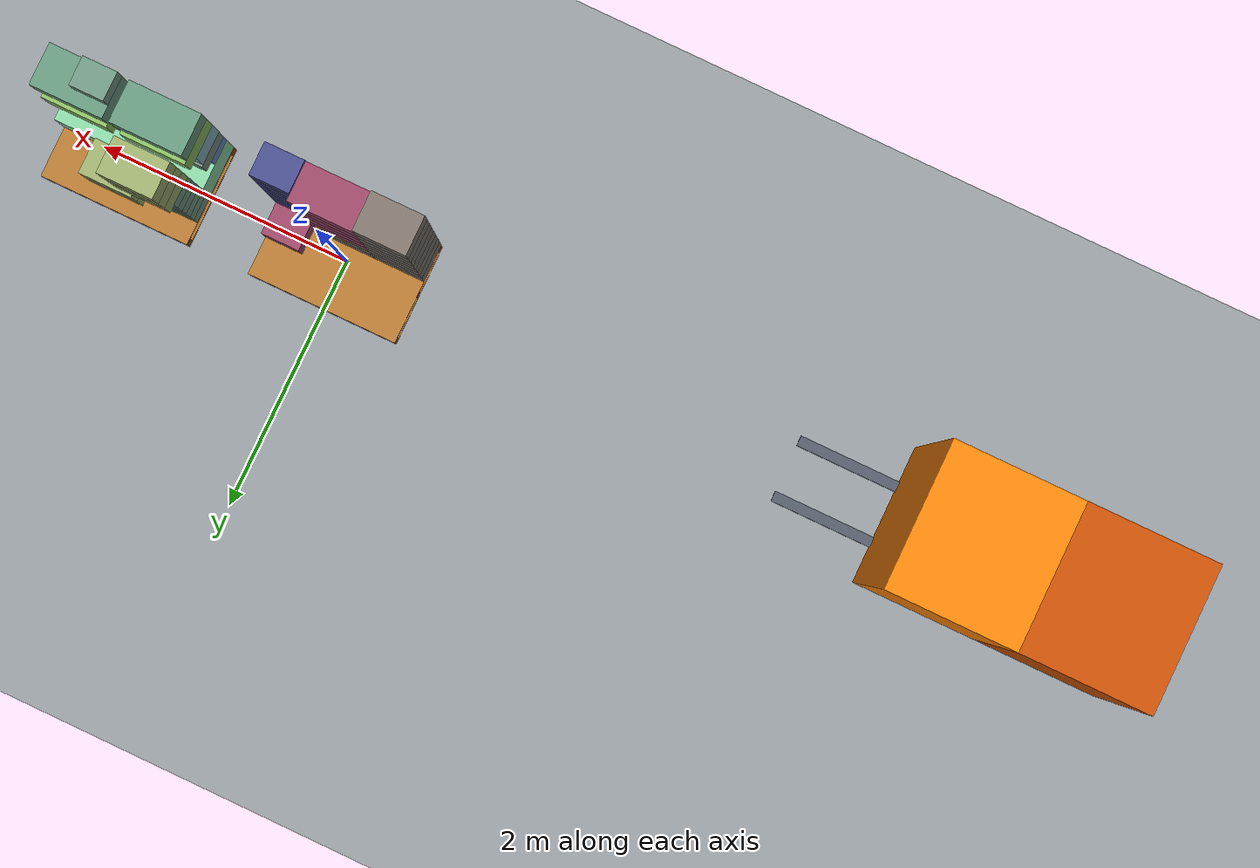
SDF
<?xml version="1.0"?>
<sdf version="1.10">
  <world name="pallet_stacker_world">
    <gravity>0 0 -9.81</gravity>
    <physics name="pallet_stacker_physics" type="ignored">
      <max_step_size>0.005</max_step_size>
      <real_time_factor>1</real_time_factor>
    </physics>
    <plugin filename="gz-sim-physics-system" name="gz::sim::systems::Physics"/>
    <plugin filename="gz-sim-user-commands-system" name="gz::sim::systems::UserCommands"/>
    <plugin filename="gz-sim-scene-broadcaster-system" name="gz::sim::systems::SceneBroadcaster"/>
    <scene>
      <ambient>0.65 0.65 0.65 1</ambient>
      <background>0.78 0.8 0.84 1</background>
      <shadows>false</shadows>
      <grid>true</grid>
    </scene>
    <gui fullscreen="0">
      <plugin filename="MinimalScene" name="3D View">
        <gz-gui>
          <title>3D View</title>
          <property type="bool" key="showTitleBar">false</property>
          <property type="string" key="state">docked</property>
        </gz-gui>
        <engine>ogre2</engine>
        <scene>scene</scene>
        <ambient_light>0.65 0.65 0.65 1</ambient_light>
        <background_color>0.78 0.8 0.84 1</background_color>
        <camera_pose>-8.505 -4.7542 5.9248 0 0.52 0.72</camera_pose>
        <camera_clip>
          <near>0.1</near>
          <far>500</far>
        </camera_clip>
      </plugin>
      <plugin filename="GzSceneManager" name="Scene Manager"/>
      <plugin filename="InteractiveViewControl" name="Interactive view control"/>
      <plugin filename="CameraTracking" name="Camera tracking"/>
      <plugin filename="MarkerManager" name="Marker manager"/>
      <plugin filename="SelectEntities" name="Select entities"/>
      <plugin filename="EntityContextMenuPlugin" name="Entity context menu"/>
      <plugin filename="VisualizationCapabilities" name="Visualization capabilities"/>
      <plugin filename="WorldControl" name="World control">
        <gz-gui>
          <title>World control</title>
          <property type="bool" key="showTitleBar">false</property>
          <property type="bool" key="resizable">false</property>
          <property type="double" key="height">72</property>
          <property type="double" key="width">121</property>
          <property type="string" key="state">floating</property>
          <anchors target="3D View">
            <line own="left" target="left"/>
            <line own="bottom" target="bottom"/>
          </anchors>
        </gz-gui>
        <play_pause>true</play_pause>
        <step>true</step>
        <start_paused>false</start_paused>
        <service>/world/pallet_stacker_world/control</service>
        <stats_topic>/world/pallet_stacker_world/stats</stats_topic>
      </plugin>
      <plugin filename="WorldStats" name="World stats">
        <gz-gui>
          <title>World stats</title>
          <property type="bool" key="showTitleBar">false</property>
          <property type="bool" key="resizable">false</property>
          <property type="double" key="height">110</property>
          <property type="double" key="width">290</property>
          <property type="string" key="state">floating</property>
          <anchors target="3D View">
            <line own="right" target="right"/>
            <line own="bottom" target="bottom"/>
          </anchors>
        </gz-gui>
        <sim_time>true</sim_time>
        <real_time>true</real_time>
        <real_time_factor>true</real_time_factor>
        <iterations>true</iterations>
        <topic>/world/pallet_stacker_world/stats</topic>
      </plugin>
      <plugin filename="EntityTree" name="Entity tree"/>
      <plugin filename="ForkliftTeleop" name="Forklift controls">
        <gz-gui>
          <title>Forklift controls</title>
          <property type="double" key="width">360</property>
          <property type="double" key="height">245</property>
          <property type="string" key="state">floating</property>
          <anchors target="3D View">
            <line own="right" target="right"/>
            <line own="top" target="top"/>
          </anchors>
        </gz-gui>
        <drive_topic>/forklift/cmd_vel</drive_topic>
        <fork_topic>/forklift/fork_position</fork_topic>
        <world_control_service>/world/pallet_stacker_world/control</world_control_service>
        <max_linear_velocity>3</max_linear_velocity>
        <max_angular_velocity>0.75</max_angular_velocity>
        <max_linear_acceleration>1</max_linear_acceleration>
        <max_angular_acceleration>1.5</max_angular_acceleration>
        <max_fork_velocity>0.5</max_fork_velocity>
        <fork_minimum>0</fork_minimum>
        <fork_maximum>1.8</fork_maximum>
        <fork_initial>0</fork_initial>
        <update_rate_hz>50</update_rate_hz>
        <auto_start>true</auto_start>
        <auto_start_retry_interval_ms>250</auto_start_retry_interval_ms>
        <auto_start_request_timeout_ms>100</auto_start_request_timeout_ms>
        <auto_start_max_attempts>60</auto_start_max_attempts>
        <forward_key>87</forward_key>
        <forward_label>W</forward_label>
        <reverse_key>83</reverse_key>
        <reverse_label>S</reverse_label>
        <left_key>65</left_key>
        <left_label>A</left_label>
        <right_key>68</right_key>
        <right_label>D</right_label>
        <lift_key>16777235</lift_key>
        <lift_label>Up</lift_label>
        <lower_key>16777237</lower_key>
        <lower_label>Down</lower_label>
        <stop_key>32</stop_key>
        <stop_label>Space</stop_label>
      </plugin>
    </gui>
    <light type="directional" name="sun">
      <pose>0 0 10 0 0 0</pose>
      <cast_shadows>false</cast_shadows>
      <direction>-0.5 0.2 -1</direction>
      <diffuse>0.9 0.9 0.9 1</diffuse>
      <specular>0.15 0.15 0.15 1</specular>
    </light>
    <model name="ground_plane">
      <static>true</static>
      <pose>-2.022 0 0 0 0 0</pose>
      <link name="link">
        <collision name="collision">
        <max_contacts>4</max_contacts>
        <geometry>
            <plane><normal>0 0 1</normal><size>20 20</size></plane>
          </geometry>
          <surface>
            <friction>
              <ode><mu>0.8</mu><mu2>0.8</mu2></ode>
              <bullet><friction>0.8</friction><friction2>0.8</friction2></bullet>
            </friction>
            <bounce>
              <restitution_coefficient>0</restitution_coefficient>
              <threshold>100000</threshold>
            </bounce>
            <contact>
              <ode>
                <kp>1000000</kp>
                <kd>100</kd>
                <max_vel>1</max_vel>
                <min_depth>0.0005</min_depth>
              </ode>
            </contact>
          </surface>
        </collision>
        <visual name="visual">
          <geometry>
            <plane><normal>0 0 1</normal><size>20 20</size></plane>
          </geometry>
          <material><ambient>0.58 0.6 0.62 1</ambient><diffuse>0.58 0.6 0.62 1</diffuse></material>
        </visual>
      </link>
    </model>
    <model name="pallet_01_PALLET_001" canonical_link="body">
      <pose>0 0 0.001 0 0 0</pose>
      <static>false</static>
      <self_collide>false</self_collide>
      <allow_auto_disable>true</allow_auto_disable>
      <frame name="loading_surface" attached_to="body">
        <pose relative_to="body">0 0 0.144 0 0 0</pose>
      </frame>
      <link name="body">
        <gravity>true</gravity>
        <kinematic>false</kinematic>
        <inertial>
          <pose>0 0 0.072 0 0 0</pose>
          <mass>25</mass>
          <inertia>
            <ixx>1.70896776228</ixx>
            <ixy>0</ixy>
            <ixz>0</ixz>
            <iyy>3.07216082337</iyy>
            <iyz>0</iyz>
            <izz>4.63680693891</izz>
          </inertia>
        </inertial>
        <collision name="bottom_deck_collision">
          <max_contacts>4</max_contacts>
          <pose>0 0 0.011 0 0 0</pose>
          <geometry>
            <box>
              <size>1.2 0.8 0.022</size>
            </box>
          </geometry>
          <surface>
            <friction>
              <ode>
                <mu>0.65</mu>
                <mu2>0.65</mu2>
              </ode>
              <bullet>
                <friction>0.65</friction>
                <friction2>0.65</friction2>
              </bullet>
            </friction>
            <bounce>
              <restitution_coefficient>0</restitution_coefficient>
              <threshold>100000</threshold>
            </bounce>
            <contact>
              <ode>
                <kp>1000000</kp>
                <kd>100</kd>
                <max_vel>1</max_vel>
                <min_depth>0.0005</min_depth>
              </ode>
            </contact>
          </surface>
        </collision>
        <visual name="bottom_deck_visual">
          <pose>0 0 0.011 0 0 0</pose>
          <geometry>
            <box>
              <size>1.2 0.8 0.022</size>
            </box>
          </geometry>
          <material>
            <ambient>0.46 0.28 0.10 1</ambient>
            <diffuse>0.64 0.42 0.18 1</diffuse>
            <specular>0.03 0.03 0.03 1</specular>
          </material>
        </visual>
        <collision name="left_stringer_collision">
          <max_contacts>4</max_contacts>
          <pose>0 -0.375 0.072 0 0 0</pose>
          <geometry>
            <box>
              <size>1.2 0.05 0.1</size>
            </box>
          </geometry>
          <surface>
            <friction>
              <ode>
                <mu>0.65</mu>
                <mu2>0.65</mu2>
              </ode>
              <bullet>
                <friction>0.65</friction>
                <friction2>0.65</friction2>
              </bullet>
            </friction>
            <bounce>
              <restitution_coefficient>0</restitution_coefficient>
              <threshold>100000</threshold>
            </bounce>
            <contact>
              <ode>
                <kp>1000000</kp>
                <kd>100</kd>
                <max_vel>1</max_vel>
                <min_depth>0.0005</min_depth>
              </ode>
            </contact>
          </surface>
        </collision>
        <visual name="left_stringer_visual">
          <pose>0 -0.375 0.072 0 0 0</pose>
          <geometry>
            <box>
              <size>1.2 0.05 0.1</size>
            </box>
          </geometry>
          <material>
            <ambient>0.42 0.25 0.09 1</ambient>
            <diffuse>0.58 0.36 0.14 1</diffuse>
            <specular>0.03 0.03 0.03 1</specular>
          </material>
        </visual>
        <collision name="centre_stringer_collision">
          <max_contacts>4</max_contacts>
          <pose>0 0 0.072 0 0 0</pose>
          <geometry>
            <box>
              <size>1.2 0.05 0.1</size>
            </box>
          </geometry>
          <surface>
            <friction>
              <ode>
                <mu>0.65</mu>
                <mu2>0.65</mu2>
              </ode>
              <bullet>
                <friction>0.65</friction>
                <friction2>0.65</friction2>
              </bullet>
            </friction>
            <bounce>
              <restitution_coefficient>0</restitution_coefficient>
              <threshold>100000</threshold>
            </bounce>
            <contact>
              <ode>
                <kp>1000000</kp>
                <kd>100</kd>
                <max_vel>1</max_vel>
                <min_depth>0.0005</min_depth>
              </ode>
            </contact>
          </surface>
        </collision>
        <visual name="centre_stringer_visual">
          <pose>0 0 0.072 0 0 0</pose>
          <geometry>
            <box>
              <size>1.2 0.05 0.1</size>
            </box>
          </geometry>
          <material>
            <ambient>0.42 0.25 0.09 1</ambient>
            <diffuse>0.58 0.36 0.14 1</diffuse>
            <specular>0.03 0.03 0.03 1</specular>
          </material>
        </visual>
        <collision name="right_stringer_collision">
          <max_contacts>4</max_contacts>
          <pose>0 0.375 0.072 0 0 0</pose>
          <geometry>
            <box>
              <size>1.2 0.05 0.1</size>
            </box>
          </geometry>
          <surface>
            <friction>
              <ode>
                <mu>0.65</mu>
                <mu2>0.65</mu2>
              </ode>
              <bullet>
                <friction>0.65</friction>
                <friction2>0.65</friction2>
              </bullet>
            </friction>
            <bounce>
              <restitution_coefficient>0</restitution_coefficient>
              <threshold>100000</threshold>
            </bounce>
            <contact>
              <ode>
                <kp>1000000</kp>
                <kd>100</kd>
                <max_vel>1</max_vel>
                <min_depth>0.0005</min_depth>
              </ode>
            </contact>
          </surface>
        </collision>
        <visual name="right_stringer_visual">
          <pose>0 0.375 0.072 0 0 0</pose>
          <geometry>
            <box>
              <size>1.2 0.05 0.1</size>
            </box>
          </geometry>
          <material>
            <ambient>0.42 0.25 0.09 1</ambient>
            <diffuse>0.58 0.36 0.14 1</diffuse>
            <specular>0.03 0.03 0.03 1</specular>
          </material>
        </visual>
        <collision name="top_deck_collision">
          <max_contacts>4</max_contacts>
          <pose>0 0 0.133 0 0 0</pose>
          <geometry>
            <box>
              <size>1.2 0.8 0.022</size>
            </box>
          </geometry>
          <surface>
            <friction>
              <ode>
                <mu>0.65</mu>
                <mu2>0.65</mu2>
              </ode>
              <bullet>
                <friction>0.65</friction>
                <friction2>0.65</friction2>
              </bullet>
            </friction>
            <bounce>
              <restitution_coefficient>0</restitution_coefficient>
              <threshold>100000</threshold>
            </bounce>
            <contact>
              <ode>
                <kp>1000000</kp>
                <kd>100</kd>
                <max_vel>1</max_vel>
                <min_depth>0.0005</min_depth>
              </ode>
            </contact>
          </surface>
        </collision>
        <visual name="top_deck_visual">
          <pose>0 0 0.133 0 0 0</pose>
          <geometry>
            <box>
              <size>1.2 0.8 0.022</size>
            </box>
          </geometry>
          <material>
            <ambient>0.50 0.31 0.11 1</ambient>
            <diffuse>0.70 0.47 0.20 1</diffuse>
            <specular>0.03 0.03 0.03 1</specular>
          </material>
        </visual>
      </link>
    </model>
    <model name="box_p01_0001_MILK_001">
      <pose>-0.4 -0.25 0.256 0 0 0</pose>
      <static>false</static>
      <self_collide>false</self_collide>
      <allow_auto_disable>true</allow_auto_disable>
      <link name="body">
        <gravity>true</gravity>
        <inertial>
          <mass>12</mass>
          <inertia>
            <ixx>0.1384</ixx><ixy>0</ixy><ixz>0</ixz>
            <iyy>0.2084</iyy><iyz>0</iyz><izz>0.25</izz>
          </inertia>
        </inertial>
        <collision name="collision">
            <max_contacts>4</max_contacts>
            <geometry>
                <box><size>0.4 0.3 0.22</size></box>
            </geometry>
          <surface>
            <friction>
              <ode><mu>0.55</mu><mu2>0.55</mu2></ode>
              <bullet><friction>0.55</friction><friction2>0.55</friction2></bullet>
            </friction>
            <bounce>
              <restitution_coefficient>0</restitution_coefficient>
              <threshold>100000</threshold>
            </bounce>
            <contact>
              <ode>
                <kp>1000000</kp>
                <kd>100</kd>
                <max_vel>1</max_vel>
                <min_depth>0.0005</min_depth>
              </ode>
            </contact>
          </surface>
        </collision>
        <visual name="visual">
          <geometry>
            <box><size>0.4 0.3 0.22</size></box>
          </geometry>
          <material>
            <ambient>0.370588235294 0.344117647059 0.317647058824 1</ambient>
            <diffuse>0.494117647059 0.458823529412 0.423529411765 1</diffuse>
            <specular>0.08 0.08 0.08 1</specular>
          </material>
        </visual>
      </link>
    </model>
    <model name="box_p01_0002_MILK_002">
      <pose>-0.4 -0.25 0.476 0 0 0</pose>
      <static>false</static>
      <self_collide>false</self_collide>
      <allow_auto_disable>true</allow_auto_disable>
      <link name="body">
        <gravity>true</gravity>
        <inertial>
          <mass>12</mass>
          <inertia>
            <ixx>0.1384</ixx><ixy>0</ixy><ixz>0</ixz>
            <iyy>0.2084</iyy><iyz>0</iyz><izz>0.25</izz>
          </inertia>
        </inertial>
        <collision name="collision">
            <max_contacts>4</max_contacts>
            <geometry>
                <box><size>0.4 0.3 0.22</size></box>
            </geometry>
          <surface>
            <friction>
              <ode><mu>0.55</mu><mu2>0.55</mu2></ode>
              <bullet><friction>0.55</friction><friction2>0.55</friction2></bullet>
            </friction>
            <bounce>
              <restitution_coefficient>0</restitution_coefficient>
              <threshold>100000</threshold>
            </bounce>
            <contact>
              <ode>
                <kp>1000000</kp>
                <kd>100</kd>
                <max_vel>1</max_vel>
                <min_depth>0.0005</min_depth>
              </ode>
            </contact>
          </surface>
        </collision>
        <visual name="visual">
          <geometry>
            <box><size>0.4 0.3 0.22</size></box>
          </geometry>
          <material>
            <ambient>0.370588235294 0.344117647059 0.317647058824 1</ambient>
            <diffuse>0.494117647059 0.458823529412 0.423529411765 1</diffuse>
            <specular>0.08 0.08 0.08 1</specular>
          </material>
        </visual>
      </link>
    </model>
    <model name="box_p01_0003_MILK_003">
      <pose>-0.4 -0.25 0.696 0 0 0</pose>
      <static>false</static>
      <self_collide>false</self_collide>
      <allow_auto_disable>true</allow_auto_disable>
      <link name="body">
        <gravity>true</gravity>
        <inertial>
          <mass>12</mass>
          <inertia>
            <ixx>0.1384</ixx><ixy>0</ixy><ixz>0</ixz>
            <iyy>0.2084</iyy><iyz>0</iyz><izz>0.25</izz>
          </inertia>
        </inertial>
        <collision name="collision">
            <max_contacts>4</max_contacts>
            <geometry>
                <box><size>0.4 0.3 0.22</size></box>
            </geometry>
          <surface>
            <friction>
              <ode><mu>0.55</mu><mu2>0.55</mu2></ode>
              <bullet><friction>0.55</friction><friction2>0.55</friction2></bullet>
            </friction>
            <bounce>
              <restitution_coefficient>0</restitution_coefficient>
              <threshold>100000</threshold>
            </bounce>
            <contact>
              <ode>
                <kp>1000000</kp>
                <kd>100</kd>
                <max_vel>1</max_vel>
                <min_depth>0.0005</min_depth>
              </ode>
            </contact>
          </surface>
        </collision>
        <visual name="visual">
          <geometry>
            <box><size>0.4 0.3 0.22</size></box>
          </geometry>
          <material>
            <ambient>0.370588235294 0.344117647059 0.317647058824 1</ambient>
            <diffuse>0.494117647059 0.458823529412 0.423529411765 1</diffuse>
            <specular>0.08 0.08 0.08 1</specular>
          </material>
        </visual>
      </link>
    </model>
    <model name="box_p01_0004_MILK_004">
      <pose>-0.4 -0.25 0.916 0 0 0</pose>
      <static>false</static>
      <self_collide>false</self_collide>
      <allow_auto_disable>true</allow_auto_disable>
      <link name="body">
        <gravity>true</gravity>
        <inertial>
          <mass>12</mass>
          <inertia>
            <ixx>0.1384</ixx><ixy>0</ixy><ixz>0</ixz>
            <iyy>0.2084</iyy><iyz>0</iyz><izz>0.25</izz>
          </inertia>
        </inertial>
        <collision name="collision">
            <max_contacts>4</max_contacts>
            <geometry>
                <box><size>0.4 0.3 0.22</size></box>
            </geometry>
          <surface>
            <friction>
              <ode><mu>0.55</mu><mu2>0.55</mu2></ode>
              <bullet><friction>0.55</friction><friction2>0.55</friction2></bullet>
            </friction>
            <bounce>
              <restitution_coefficient>0</restitution_coefficient>
              <threshold>100000</threshold>
            </bounce>
            <contact>
              <ode>
                <kp>1000000</kp>
                <kd>100</kd>
                <max_vel>1</max_vel>
                <min_depth>0.0005</min_depth>
              </ode>
            </contact>
          </surface>
        </collision>
        <visual name="visual">
          <geometry>
            <box><size>0.4 0.3 0.22</size></box>
          </geometry>
          <material>
            <ambient>0.370588235294 0.344117647059 0.317647058824 1</ambient>
            <diffuse>0.494117647059 0.458823529412 0.423529411765 1</diffuse>
            <specular>0.08 0.08 0.08 1</specular>
          </material>
        </visual>
      </link>
    </model>
    <model name="box_p01_0005_MILK_005">
      <pose>-0.4 -0.25 1.136 0 0 0</pose>
      <static>false</static>
      <self_collide>false</self_collide>
      <allow_auto_disable>true</allow_auto_disable>
      <link name="body">
        <gravity>true</gravity>
        <inertial>
          <mass>12</mass>
          <inertia>
            <ixx>0.1384</ixx><ixy>0</ixy><ixz>0</ixz>
            <iyy>0.2084</iyy><iyz>0</iyz><izz>0.25</izz>
          </inertia>
        </inertial>
        <collision name="collision">
            <max_contacts>4</max_contacts>
            <geometry>
                <box><size>0.4 0.3 0.22</size></box>
            </geometry>
          <surface>
            <friction>
              <ode><mu>0.55</mu><mu2>0.55</mu2></ode>
              <bullet><friction>0.55</friction><friction2>0.55</friction2></bullet>
            </friction>
            <bounce>
              <restitution_coefficient>0</restitution_coefficient>
              <threshold>100000</threshold>
            </bounce>
            <contact>
              <ode>
                <kp>1000000</kp>
                <kd>100</kd>
                <max_vel>1</max_vel>
                <min_depth>0.0005</min_depth>
              </ode>
            </contact>
          </surface>
        </collision>
        <visual name="visual">
          <geometry>
            <box><size>0.4 0.3 0.22</size></box>
          </geometry>
          <material>
            <ambient>0.370588235294 0.344117647059 0.317647058824 1</ambient>
            <diffuse>0.494117647059 0.458823529412 0.423529411765 1</diffuse>
            <specular>0.08 0.08 0.08 1</specular>
          </material>
        </visual>
      </link>
    </model>
    <model name="box_p01_0006_MILK_006">
      <pose>-0.4 -0.25 1.356 0 0 0</pose>
      <static>false</static>
      <self_collide>false</self_collide>
      <allow_auto_disable>true</allow_auto_disable>
      <link name="body">
        <gravity>true</gravity>
        <inertial>
          <mass>12</mass>
          <inertia>
            <ixx>0.1384</ixx><ixy>0</ixy><ixz>0</ixz>
            <iyy>0.2084</iyy><iyz>0</iyz><izz>0.25</izz>
          </inertia>
        </inertial>
        <collision name="collision">
            <max_contacts>4</max_contacts>
            <geometry>
                <box><size>0.4 0.3 0.22</size></box>
            </geometry>
          <surface>
            <friction>
              <ode><mu>0.55</mu><mu2>0.55</mu2></ode>
              <bullet><friction>0.55</friction><friction2>0.55</friction2></bullet>
            </friction>
            <bounce>
              <restitution_coefficient>0</restitution_coefficient>
              <threshold>100000</threshold>
            </bounce>
            <contact>
              <ode>
                <kp>1000000</kp>
                <kd>100</kd>
                <max_vel>1</max_vel>
                <min_depth>0.0005</min_depth>
              </ode>
            </contact>
          </surface>
        </collision>
        <visual name="visual">
          <geometry>
            <box><size>0.4 0.3 0.22</size></box>
          </geometry>
          <material>
            <ambient>0.370588235294 0.344117647059 0.317647058824 1</ambient>
            <diffuse>0.494117647059 0.458823529412 0.423529411765 1</diffuse>
            <specular>0.08 0.08 0.08 1</specular>
          </material>
        </visual>
      </link>
    </model>
    <model name="box_p01_0007_MILK_007">
      <pose>-0.4 -0.25 1.576 0 0 0</pose>
      <static>false</static>
      <self_collide>false</self_collide>
      <allow_auto_disable>true</allow_auto_disable>
      <link name="body">
        <gravity>true</gravity>
        <inertial>
          <mass>12</mass>
          <inertia>
            <ixx>0.1384</ixx><ixy>0</ixy><ixz>0</ixz>
            <iyy>0.2084</iyy><iyz>0</iyz><izz>0.25</izz>
          </inertia>
        </inertial>
        <collision name="collision">
            <max_contacts>4</max_contacts>
            <geometry>
                <box><size>0.4 0.3 0.22</size></box>
            </geometry>
          <surface>
            <friction>
              <ode><mu>0.55</mu><mu2>0.55</mu2></ode>
              <bullet><friction>0.55</friction><friction2>0.55</friction2></bullet>
            </friction>
            <bounce>
              <restitution_coefficient>0</restitution_coefficient>
              <threshold>100000</threshold>
            </bounce>
            <contact>
              <ode>
                <kp>1000000</kp>
                <kd>100</kd>
                <max_vel>1</max_vel>
                <min_depth>0.0005</min_depth>
              </ode>
            </contact>
          </surface>
        </collision>
        <visual name="visual">
          <geometry>
            <box><size>0.4 0.3 0.22</size></box>
          </geometry>
          <material>
            <ambient>0.370588235294 0.344117647059 0.317647058824 1</ambient>
            <diffuse>0.494117647059 0.458823529412 0.423529411765 1</diffuse>
            <specular>0.08 0.08 0.08 1</specular>
          </material>
        </visual>
      </link>
    </model>
    <model name="box_p01_0008_MILK_008">
      <pose>-0.4 -0.25 1.796 0 0 0</pose>
      <static>false</static>
      <self_collide>false</self_collide>
      <allow_auto_disable>true</allow_auto_disable>
      <link name="body">
        <gravity>true</gravity>
        <inertial>
          <mass>12</mass>
          <inertia>
            <ixx>0.1384</ixx><ixy>0</ixy><ixz>0</ixz>
            <iyy>0.2084</iyy><iyz>0</iyz><izz>0.25</izz>
          </inertia>
        </inertial>
        <collision name="collision">
            <max_contacts>4</max_contacts>
            <geometry>
                <box><size>0.4 0.3 0.22</size></box>
            </geometry>
          <surface>
            <friction>
              <ode><mu>0.55</mu><mu2>0.55</mu2></ode>
              <bullet><friction>0.55</friction><friction2>0.55</friction2></bullet>
            </friction>
            <bounce>
              <restitution_coefficient>0</restitution_coefficient>
              <threshold>100000</threshold>
            </bounce>
            <contact>
              <ode>
                <kp>1000000</kp>
                <kd>100</kd>
                <max_vel>1</max_vel>
                <min_depth>0.0005</min_depth>
              </ode>
            </contact>
          </surface>
        </collision>
        <visual name="visual">
          <geometry>
            <box><size>0.4 0.3 0.22</size></box>
          </geometry>
          <material>
            <ambient>0.370588235294 0.344117647059 0.317647058824 1</ambient>
            <diffuse>0.494117647059 0.458823529412 0.423529411765 1</diffuse>
            <specular>0.08 0.08 0.08 1</specular>
          </material>
        </visual>
      </link>
    </model>
    <model name="box_p01_0009_MILK_009">
      <pose>5.55111512313e-17 -0.25 0.256 0 0 0</pose>
      <static>false</static>
      <self_collide>false</self_collide>
      <allow_auto_disable>true</allow_auto_disable>
      <link name="body">
        <gravity>true</gravity>
        <inertial>
          <mass>12</mass>
          <inertia>
            <ixx>0.1384</ixx><ixy>0</ixy><ixz>0</ixz>
            <iyy>0.2084</iyy><iyz>0</iyz><izz>0.25</izz>
          </inertia>
        </inertial>
        <collision name="collision">
            <max_contacts>4</max_contacts>
            <geometry>
                <box><size>0.4 0.3 0.22</size></box>
            </geometry>
          <surface>
            <friction>
              <ode><mu>0.55</mu><mu2>0.55</mu2></ode>
              <bullet><friction>0.55</friction><friction2>0.55</friction2></bullet>
            </friction>
            <bounce>
              <restitution_coefficient>0</restitution_coefficient>
              <threshold>100000</threshold>
            </bounce>
            <contact>
              <ode>
                <kp>1000000</kp>
                <kd>100</kd>
                <max_vel>1</max_vel>
                <min_depth>0.0005</min_depth>
              </ode>
            </contact>
          </surface>
        </collision>
        <visual name="visual">
          <geometry>
            <box><size>0.4 0.3 0.22</size></box>
          </geometry>
          <material>
            <ambient>0.370588235294 0.344117647059 0.317647058824 1</ambient>
            <diffuse>0.494117647059 0.458823529412 0.423529411765 1</diffuse>
            <specular>0.08 0.08 0.08 1</specular>
          </material>
        </visual>
      </link>
    </model>
    <model name="box_p01_0010_MILK_010">
      <pose>5.55111512313e-17 -0.25 0.476 0 0 0</pose>
      <static>false</static>
      <self_collide>false</self_collide>
      <allow_auto_disable>true</allow_auto_disable>
      <link name="body">
        <gravity>true</gravity>
        <inertial>
          <mass>12</mass>
          <inertia>
            <ixx>0.1384</ixx><ixy>0</ixy><ixz>0</ixz>
            <iyy>0.2084</iyy><iyz>0</iyz><izz>0.25</izz>
          </inertia>
        </inertial>
        <collision name="collision">
            <max_contacts>4</max_contacts>
            <geometry>
                <box><size>0.4 0.3 0.22</size></box>
            </geometry>
          <surface>
            <friction>
              <ode><mu>0.55</mu><mu2>0.55</mu2></ode>
              <bullet><friction>0.55</friction><friction2>0.55</friction2></bullet>
            </friction>
            <bounce>
              <restitution_coefficient>0</restitution_coefficient>
              <threshold>100000</threshold>
            </bounce>
            <contact>
              <ode>
                <kp>1000000</kp>
                <kd>100</kd>
                <max_vel>1</max_vel>
                <min_depth>0.0005</min_depth>
              </ode>
            </contact>
          </surface>
        </collision>
        <visual name="visual">
          <geometry>
            <box><size>0.4 0.3 0.22</size></box>
          </geometry>
          <material>
            <ambient>0.370588235294 0.344117647059 0.317647058824 1</ambient>
            <diffuse>0.494117647059 0.458823529412 0.423529411765 1</diffuse>
            <specular>0.08 0.08 0.08 1</specular>
          </material>
        </visual>
      </link>
    </model>
    <model name="box_p01_0011_CEREAL_011">
      <pose>0.05 -0.25 0.706 0 0 0</pose>
      <static>false</static>
      <self_collide>false</self_collide>
      <allow_auto_disable>true</allow_auto_disable>
      <link name="body">
        <gravity>true</gravity>
        <inertial>
          <mass>4</mass>
          <inertia>
            <ixx>0.0492</ixx><ixy>0</ixy><ixz>0</ixz>
            <iyy>0.102533333333</iyy><iyz>0</iyz><izz>0.113333333333</izz>
          </inertia>
        </inertial>
        <collision name="collision">
            <max_contacts>4</max_contacts>
            <geometry>
                <box><size>0.5 0.3 0.24</size></box>
            </geometry>
          <surface>
            <friction>
              <ode><mu>0.55</mu><mu2>0.55</mu2></ode>
              <bullet><friction>0.55</friction><friction2>0.55</friction2></bullet>
            </friction>
            <bounce>
              <restitution_coefficient>0</restitution_coefficient>
              <threshold>100000</threshold>
            </bounce>
            <contact>
              <ode>
                <kp>1000000</kp>
                <kd>100</kd>
                <max_vel>1</max_vel>
                <min_depth>0.0005</min_depth>
              </ode>
            </contact>
          </surface>
        </collision>
        <visual name="visual">
          <geometry>
            <box><size>0.5 0.3 0.24</size></box>
          </geometry>
          <material>
            <ambient>0.45 0.208823529412 0.302941176471 1</ambient>
            <diffuse>0.6 0.278431372549 0.403921568627 1</diffuse>
            <specular>0.08 0.08 0.08 1</specular>
          </material>
        </visual>
      </link>
    </model>
    <model name="box_p01_0012_CEREAL_012">
      <pose>0.05 -0.25 0.946 0 0 0</pose>
      <static>false</static>
      <self_collide>false</self_collide>
      <allow_auto_disable>true</allow_auto_disable>
      <link name="body">
        <gravity>true</gravity>
        <inertial>
          <mass>4</mass>
          <inertia>
            <ixx>0.0492</ixx><ixy>0</ixy><ixz>0</ixz>
            <iyy>0.102533333333</iyy><iyz>0</iyz><izz>0.113333333333</izz>
          </inertia>
        </inertial>
        <collision name="collision">
            <max_contacts>4</max_contacts>
            <geometry>
                <box><size>0.5 0.3 0.24</size></box>
            </geometry>
          <surface>
            <friction>
              <ode><mu>0.55</mu><mu2>0.55</mu2></ode>
              <bullet><friction>0.55</friction><friction2>0.55</friction2></bullet>
            </friction>
            <bounce>
              <restitution_coefficient>0</restitution_coefficient>
              <threshold>100000</threshold>
            </bounce>
            <contact>
              <ode>
                <kp>1000000</kp>
                <kd>100</kd>
                <max_vel>1</max_vel>
                <min_depth>0.0005</min_depth>
              </ode>
            </contact>
          </surface>
        </collision>
        <visual name="visual">
          <geometry>
            <box><size>0.5 0.3 0.24</size></box>
          </geometry>
          <material>
            <ambient>0.45 0.208823529412 0.302941176471 1</ambient>
            <diffuse>0.6 0.278431372549 0.403921568627 1</diffuse>
            <specular>0.08 0.08 0.08 1</specular>
          </material>
        </visual>
      </link>
    </model>
    <model name="box_p01_0013_CEREAL_013">
      <pose>0.05 -0.25 1.186 0 0 0</pose>
      <static>false</static>
      <self_collide>false</self_collide>
      <allow_auto_disable>true</allow_auto_disable>
      <link name="body">
        <gravity>true</gravity>
        <inertial>
          <mass>4</mass>
          <inertia>
            <ixx>0.0492</ixx><ixy>0</ixy><ixz>0</ixz>
            <iyy>0.102533333333</iyy><iyz>0</iyz><izz>0.113333333333</izz>
          </inertia>
        </inertial>
        <collision name="collision">
            <max_contacts>4</max_contacts>
            <geometry>
                <box><size>0.5 0.3 0.24</size></box>
            </geometry>
          <surface>
            <friction>
              <ode><mu>0.55</mu><mu2>0.55</mu2></ode>
              <bullet><friction>0.55</friction><friction2>0.55</friction2></bullet>
            </friction>
            <bounce>
              <restitution_coefficient>0</restitution_coefficient>
              <threshold>100000</threshold>
            </bounce>
            <contact>
              <ode>
                <kp>1000000</kp>
                <kd>100</kd>
                <max_vel>1</max_vel>
                <min_depth>0.0005</min_depth>
              </ode>
            </contact>
          </surface>
        </collision>
        <visual name="visual">
          <geometry>
            <box><size>0.5 0.3 0.24</size></box>
          </geometry>
          <material>
            <ambient>0.45 0.208823529412 0.302941176471 1</ambient>
            <diffuse>0.6 0.278431372549 0.403921568627 1</diffuse>
            <specular>0.08 0.08 0.08 1</specular>
          </material>
        </visual>
      </link>
    </model>
    <model name="box_p01_0014_CEREAL_014">
      <pose>0.05 -0.25 1.426 0 0 0</pose>
      <static>false</static>
      <self_collide>false</self_collide>
      <allow_auto_disable>true</allow_auto_disable>
      <link name="body">
        <gravity>true</gravity>
        <inertial>
          <mass>4</mass>
          <inertia>
            <ixx>0.0492</ixx><ixy>0</ixy><ixz>0</ixz>
            <iyy>0.102533333333</iyy><iyz>0</iyz><izz>0.113333333333</izz>
          </inertia>
        </inertial>
        <collision name="collision">
            <max_contacts>4</max_contacts>
            <geometry>
                <box><size>0.5 0.3 0.24</size></box>
            </geometry>
          <surface>
            <friction>
              <ode><mu>0.55</mu><mu2>0.55</mu2></ode>
              <bullet><friction>0.55</friction><friction2>0.55</friction2></bullet>
            </friction>
            <bounce>
              <restitution_coefficient>0</restitution_coefficient>
              <threshold>100000</threshold>
            </bounce>
            <contact>
              <ode>
                <kp>1000000</kp>
                <kd>100</kd>
                <max_vel>1</max_vel>
                <min_depth>0.0005</min_depth>
              </ode>
            </contact>
          </surface>
        </collision>
        <visual name="visual">
          <geometry>
            <box><size>0.5 0.3 0.24</size></box>
          </geometry>
          <material>
            <ambient>0.45 0.208823529412 0.302941176471 1</ambient>
            <diffuse>0.6 0.278431372549 0.403921568627 1</diffuse>
            <specular>0.08 0.08 0.08 1</specular>
          </material>
        </visual>
      </link>
    </model>
    <model name="box_p01_0015_CEREAL_015">
      <pose>0.05 -0.25 1.666 0 0 0</pose>
      <static>false</static>
      <self_collide>false</self_collide>
      <allow_auto_disable>true</allow_auto_disable>
      <link name="body">
        <gravity>true</gravity>
        <inertial>
          <mass>4</mass>
          <inertia>
            <ixx>0.0492</ixx><ixy>0</ixy><ixz>0</ixz>
            <iyy>0.102533333333</iyy><iyz>0</iyz><izz>0.113333333333</izz>
          </inertia>
        </inertial>
        <collision name="collision">
            <max_contacts>4</max_contacts>
            <geometry>
                <box><size>0.5 0.3 0.24</size></box>
            </geometry>
          <surface>
            <friction>
              <ode><mu>0.55</mu><mu2>0.55</mu2></ode>
              <bullet><friction>0.55</friction><friction2>0.55</friction2></bullet>
            </friction>
            <bounce>
              <restitution_coefficient>0</restitution_coefficient>
              <threshold>100000</threshold>
            </bounce>
            <contact>
              <ode>
                <kp>1000000</kp>
                <kd>100</kd>
                <max_vel>1</max_vel>
                <min_depth>0.0005</min_depth>
              </ode>
            </contact>
          </surface>
        </collision>
        <visual name="visual">
          <geometry>
            <box><size>0.5 0.3 0.24</size></box>
          </geometry>
          <material>
            <ambient>0.45 0.208823529412 0.302941176471 1</ambient>
            <diffuse>0.6 0.278431372549 0.403921568627 1</diffuse>
            <specular>0.08 0.08 0.08 1</specular>
          </material>
        </visual>
      </link>
    </model>
    <model name="box_p01_0016_CEREAL_016">
      <pose>0.45 -0.15 0.266 0 0 0</pose>
      <static>false</static>
      <self_collide>false</self_collide>
      <allow_auto_disable>true</allow_auto_disable>
      <link name="body">
        <gravity>true</gravity>
        <inertial>
          <mass>4</mass>
          <inertia>
            <ixx>0.102533333333</ixx><ixy>0</ixy><ixz>0</ixz>
            <iyy>0.0492</iyy><iyz>0</iyz><izz>0.113333333333</izz>
          </inertia>
        </inertial>
        <collision name="collision">
            <max_contacts>4</max_contacts>
            <geometry>
                <box><size>0.3 0.5 0.24</size></box>
            </geometry>
          <surface>
            <friction>
              <ode><mu>0.55</mu><mu2>0.55</mu2></ode>
              <bullet><friction>0.55</friction><friction2>0.55</friction2></bullet>
            </friction>
            <bounce>
              <restitution_coefficient>0</restitution_coefficient>
              <threshold>100000</threshold>
            </bounce>
            <contact>
              <ode>
                <kp>1000000</kp>
                <kd>100</kd>
                <max_vel>1</max_vel>
                <min_depth>0.0005</min_depth>
              </ode>
            </contact>
          </surface>
        </collision>
        <visual name="visual">
          <geometry>
            <box><size>0.3 0.5 0.24</size></box>
          </geometry>
          <material>
            <ambient>0.45 0.208823529412 0.302941176471 1</ambient>
            <diffuse>0.6 0.278431372549 0.403921568627 1</diffuse>
            <specular>0.08 0.08 0.08 1</specular>
          </material>
        </visual>
      </link>
    </model>
    <model name="box_p01_0017_CANS_017">
      <pose>0.45 -0.275 0.476 0 0 0</pose>
      <static>false</static>
      <self_collide>false</self_collide>
      <allow_auto_disable>true</allow_auto_disable>
      <link name="body">
        <gravity>true</gravity>
        <inertial>
          <mass>10</mass>
          <inertia>
            <ixx>0.0790833333333</ixx><ixy>0</ixy><ixz>0</ixz>
            <iyy>0.102</iyy><iyz>0</iyz><izz>0.127083333333</izz>
          </inertia>
        </inertial>
        <collision name="collision">
            <max_contacts>4</max_contacts>
            <geometry>
                <box><size>0.3 0.25 0.18</size></box>
            </geometry>
          <surface>
            <friction>
              <ode><mu>0.55</mu><mu2>0.55</mu2></ode>
              <bullet><friction>0.55</friction><friction2>0.55</friction2></bullet>
            </friction>
            <bounce>
              <restitution_coefficient>0</restitution_coefficient>
              <threshold>100000</threshold>
            </bounce>
            <contact>
              <ode>
                <kp>1000000</kp>
                <kd>100</kd>
                <max_vel>1</max_vel>
                <min_depth>0.0005</min_depth>
              </ode>
            </contact>
          </surface>
        </collision>
        <visual name="visual">
          <geometry>
            <box><size>0.3 0.25 0.18</size></box>
          </geometry>
          <material>
            <ambient>0.211764705882 0.229411764706 0.411764705882 1</ambient>
            <diffuse>0.282352941176 0.305882352941 0.549019607843 1</diffuse>
            <specular>0.08 0.08 0.08 1</specular>
          </material>
        </visual>
      </link>
    </model>
    <model name="box_p01_0018_CANS_018">
      <pose>0.45 -0.275 0.656 0 0 0</pose>
      <static>false</static>
      <self_collide>false</self_collide>
      <allow_auto_disable>true</allow_auto_disable>
      <link name="body">
        <gravity>true</gravity>
        <inertial>
          <mass>10</mass>
          <inertia>
            <ixx>0.0790833333333</ixx><ixy>0</ixy><ixz>0</ixz>
            <iyy>0.102</iyy><iyz>0</iyz><izz>0.127083333333</izz>
          </inertia>
        </inertial>
        <collision name="collision">
            <max_contacts>4</max_contacts>
            <geometry>
                <box><size>0.3 0.25 0.18</size></box>
            </geometry>
          <surface>
            <friction>
              <ode><mu>0.55</mu><mu2>0.55</mu2></ode>
              <bullet><friction>0.55</friction><friction2>0.55</friction2></bullet>
            </friction>
            <bounce>
              <restitution_coefficient>0</restitution_coefficient>
              <threshold>100000</threshold>
            </bounce>
            <contact>
              <ode>
                <kp>1000000</kp>
                <kd>100</kd>
                <max_vel>1</max_vel>
                <min_depth>0.0005</min_depth>
              </ode>
            </contact>
          </surface>
        </collision>
        <visual name="visual">
          <geometry>
            <box><size>0.3 0.25 0.18</size></box>
          </geometry>
          <material>
            <ambient>0.211764705882 0.229411764706 0.411764705882 1</ambient>
            <diffuse>0.282352941176 0.305882352941 0.549019607843 1</diffuse>
            <specular>0.08 0.08 0.08 1</specular>
          </material>
        </visual>
      </link>
    </model>
    <model name="box_p01_0019_CANS_019">
      <pose>0.45 -0.275 0.836 0 0 0</pose>
      <static>false</static>
      <self_collide>false</self_collide>
      <allow_auto_disable>true</allow_auto_disable>
      <link name="body">
        <gravity>true</gravity>
        <inertial>
          <mass>10</mass>
          <inertia>
            <ixx>0.0790833333333</ixx><ixy>0</ixy><ixz>0</ixz>
            <iyy>0.102</iyy><iyz>0</iyz><izz>0.127083333333</izz>
          </inertia>
        </inertial>
        <collision name="collision">
            <max_contacts>4</max_contacts>
            <geometry>
                <box><size>0.3 0.25 0.18</size></box>
            </geometry>
          <surface>
            <friction>
              <ode><mu>0.55</mu><mu2>0.55</mu2></ode>
              <bullet><friction>0.55</friction><friction2>0.55</friction2></bullet>
            </friction>
            <bounce>
              <restitution_coefficient>0</restitution_coefficient>
              <threshold>100000</threshold>
            </bounce>
            <contact>
              <ode>
                <kp>1000000</kp>
                <kd>100</kd>
                <max_vel>1</max_vel>
                <min_depth>0.0005</min_depth>
              </ode>
            </contact>
          </surface>
        </collision>
        <visual name="visual">
          <geometry>
            <box><size>0.3 0.25 0.18</size></box>
          </geometry>
          <material>
            <ambient>0.211764705882 0.229411764706 0.411764705882 1</ambient>
            <diffuse>0.282352941176 0.305882352941 0.549019607843 1</diffuse>
            <specular>0.08 0.08 0.08 1</specular>
          </material>
        </visual>
      </link>
    </model>
    <model name="box_p01_0020_CANS_020">
      <pose>0.45 -0.275 1.016 0 0 0</pose>
      <static>false</static>
      <self_collide>false</self_collide>
      <allow_auto_disable>true</allow_auto_disable>
      <link name="body">
        <gravity>true</gravity>
        <inertial>
          <mass>10</mass>
          <inertia>
            <ixx>0.0790833333333</ixx><ixy>0</ixy><ixz>0</ixz>
            <iyy>0.102</iyy><iyz>0</iyz><izz>0.127083333333</izz>
          </inertia>
        </inertial>
        <collision name="collision">
            <max_contacts>4</max_contacts>
            <geometry>
                <box><size>0.3 0.25 0.18</size></box>
            </geometry>
          <surface>
            <friction>
              <ode><mu>0.55</mu><mu2>0.55</mu2></ode>
              <bullet><friction>0.55</friction><friction2>0.55</friction2></bullet>
            </friction>
            <bounce>
              <restitution_coefficient>0</restitution_coefficient>
              <threshold>100000</threshold>
            </bounce>
            <contact>
              <ode>
                <kp>1000000</kp>
                <kd>100</kd>
                <max_vel>1</max_vel>
                <min_depth>0.0005</min_depth>
              </ode>
            </contact>
          </surface>
        </collision>
        <visual name="visual">
          <geometry>
            <box><size>0.3 0.25 0.18</size></box>
          </geometry>
          <material>
            <ambient>0.211764705882 0.229411764706 0.411764705882 1</ambient>
            <diffuse>0.282352941176 0.305882352941 0.549019607843 1</diffuse>
            <specular>0.08 0.08 0.08 1</specular>
          </material>
        </visual>
      </link>
    </model>
    <model name="box_p01_0021_CANS_021">
      <pose>0.45 -0.275 1.196 0 0 0</pose>
      <static>false</static>
      <self_collide>false</self_collide>
      <allow_auto_disable>true</allow_auto_disable>
      <link name="body">
        <gravity>true</gravity>
        <inertial>
          <mass>10</mass>
          <inertia>
            <ixx>0.0790833333333</ixx><ixy>0</ixy><ixz>0</ixz>
            <iyy>0.102</iyy><iyz>0</iyz><izz>0.127083333333</izz>
          </inertia>
        </inertial>
        <collision name="collision">
            <max_contacts>4</max_contacts>
            <geometry>
                <box><size>0.3 0.25 0.18</size></box>
            </geometry>
          <surface>
            <friction>
              <ode><mu>0.55</mu><mu2>0.55</mu2></ode>
              <bullet><friction>0.55</friction><friction2>0.55</friction2></bullet>
            </friction>
            <bounce>
              <restitution_coefficient>0</restitution_coefficient>
              <threshold>100000</threshold>
            </bounce>
            <contact>
              <ode>
                <kp>1000000</kp>
                <kd>100</kd>
                <max_vel>1</max_vel>
                <min_depth>0.0005</min_depth>
              </ode>
            </contact>
          </surface>
        </collision>
        <visual name="visual">
          <geometry>
            <box><size>0.3 0.25 0.18</size></box>
          </geometry>
          <material>
            <ambient>0.211764705882 0.229411764706 0.411764705882 1</ambient>
            <diffuse>0.282352941176 0.305882352941 0.549019607843 1</diffuse>
            <specular>0.08 0.08 0.08 1</specular>
          </material>
        </visual>
      </link>
    </model>
    <model name="box_p01_0022_CANS_022">
      <pose>0.45 -0.275 1.376 0 0 0</pose>
      <static>false</static>
      <self_collide>false</self_collide>
      <allow_auto_disable>true</allow_auto_disable>
      <link name="body">
        <gravity>true</gravity>
        <inertial>
          <mass>10</mass>
          <inertia>
            <ixx>0.0790833333333</ixx><ixy>0</ixy><ixz>0</ixz>
            <iyy>0.102</iyy><iyz>0</iyz><izz>0.127083333333</izz>
          </inertia>
        </inertial>
        <collision name="collision">
            <max_contacts>4</max_contacts>
            <geometry>
                <box><size>0.3 0.25 0.18</size></box>
            </geometry>
          <surface>
            <friction>
              <ode><mu>0.55</mu><mu2>0.55</mu2></ode>
              <bullet><friction>0.55</friction><friction2>0.55</friction2></bullet>
            </friction>
            <bounce>
              <restitution_coefficient>0</restitution_coefficient>
              <threshold>100000</threshold>
            </bounce>
            <contact>
              <ode>
                <kp>1000000</kp>
                <kd>100</kd>
                <max_vel>1</max_vel>
                <min_depth>0.0005</min_depth>
              </ode>
            </contact>
          </surface>
        </collision>
        <visual name="visual">
          <geometry>
            <box><size>0.3 0.25 0.18</size></box>
          </geometry>
          <material>
            <ambient>0.211764705882 0.229411764706 0.411764705882 1</ambient>
            <diffuse>0.282352941176 0.305882352941 0.549019607843 1</diffuse>
            <specular>0.08 0.08 0.08 1</specular>
          </material>
        </visual>
      </link>
    </model>
    <model name="box_p01_0023_CANS_023">
      <pose>0.45 -0.275 1.556 0 0 0</pose>
      <static>false</static>
      <self_collide>false</self_collide>
      <allow_auto_disable>true</allow_auto_disable>
      <link name="body">
        <gravity>true</gravity>
        <inertial>
          <mass>10</mass>
          <inertia>
            <ixx>0.0790833333333</ixx><ixy>0</ixy><ixz>0</ixz>
            <iyy>0.102</iyy><iyz>0</iyz><izz>0.127083333333</izz>
          </inertia>
        </inertial>
        <collision name="collision">
            <max_contacts>4</max_contacts>
            <geometry>
                <box><size>0.3 0.25 0.18</size></box>
            </geometry>
          <surface>
            <friction>
              <ode><mu>0.55</mu><mu2>0.55</mu2></ode>
              <bullet><friction>0.55</friction><friction2>0.55</friction2></bullet>
            </friction>
            <bounce>
              <restitution_coefficient>0</restitution_coefficient>
              <threshold>100000</threshold>
            </bounce>
            <contact>
              <ode>
                <kp>1000000</kp>
                <kd>100</kd>
                <max_vel>1</max_vel>
                <min_depth>0.0005</min_depth>
              </ode>
            </contact>
          </surface>
        </collision>
        <visual name="visual">
          <geometry>
            <box><size>0.3 0.25 0.18</size></box>
          </geometry>
          <material>
            <ambient>0.211764705882 0.229411764706 0.411764705882 1</ambient>
            <diffuse>0.282352941176 0.305882352941 0.549019607843 1</diffuse>
            <specular>0.08 0.08 0.08 1</specular>
          </material>
        </visual>
      </link>
    </model>
    <model name="box_p01_0024_CANS_024">
      <pose>0.45 -0.275 1.736 0 0 0</pose>
      <static>false</static>
      <self_collide>false</self_collide>
      <allow_auto_disable>true</allow_auto_disable>
      <link name="body">
        <gravity>true</gravity>
        <inertial>
          <mass>10</mass>
          <inertia>
            <ixx>0.0790833333333</ixx><ixy>0</ixy><ixz>0</ixz>
            <iyy>0.102</iyy><iyz>0</iyz><izz>0.127083333333</izz>
          </inertia>
        </inertial>
        <collision name="collision">
            <max_contacts>4</max_contacts>
            <geometry>
                <box><size>0.3 0.25 0.18</size></box>
            </geometry>
          <surface>
            <friction>
              <ode><mu>0.55</mu><mu2>0.55</mu2></ode>
              <bullet><friction>0.55</friction><friction2>0.55</friction2></bullet>
            </friction>
            <bounce>
              <restitution_coefficient>0</restitution_coefficient>
              <threshold>100000</threshold>
            </bounce>
            <contact>
              <ode>
                <kp>1000000</kp>
                <kd>100</kd>
                <max_vel>1</max_vel>
                <min_depth>0.0005</min_depth>
              </ode>
            </contact>
          </surface>
        </collision>
        <visual name="visual">
          <geometry>
            <box><size>0.3 0.25 0.18</size></box>
          </geometry>
          <material>
            <ambient>0.211764705882 0.229411764706 0.411764705882 1</ambient>
            <diffuse>0.282352941176 0.305882352941 0.549019607843 1</diffuse>
            <specular>0.08 0.08 0.08 1</specular>
          </material>
        </visual>
      </link>
    </model>
    <model name="pallet_02_PALLET_002" canonical_link="body">
      <pose>1.7 0 0.001 0 0 0</pose>
      <static>false</static>
      <self_collide>false</self_collide>
      <allow_auto_disable>true</allow_auto_disable>
      <frame name="loading_surface" attached_to="body">
        <pose relative_to="body">0 0 0.144 0 0 0</pose>
      </frame>
      <link name="body">
        <gravity>true</gravity>
        <kinematic>false</kinematic>
        <inertial>
          <pose>0 0 0.072 0 0 0</pose>
          <mass>25</mass>
          <inertia>
            <ixx>1.70896776228</ixx>
            <ixy>0</ixy>
            <ixz>0</ixz>
            <iyy>3.07216082337</iyy>
            <iyz>0</iyz>
            <izz>4.63680693891</izz>
          </inertia>
        </inertial>
        <collision name="bottom_deck_collision">
          <max_contacts>4</max_contacts>
          <pose>0 0 0.011 0 0 0</pose>
          <geometry>
            <box>
              <size>1.2 0.8 0.022</size>
            </box>
          </geometry>
          <surface>
            <friction>
              <ode>
                <mu>0.65</mu>
                <mu2>0.65</mu2>
              </ode>
              <bullet>
                <friction>0.65</friction>
                <friction2>0.65</friction2>
              </bullet>
            </friction>
            <bounce>
              <restitution_coefficient>0</restitution_coefficient>
              <threshold>100000</threshold>
            </bounce>
            <contact>
              <ode>
                <kp>1000000</kp>
                <kd>100</kd>
                <max_vel>1</max_vel>
                <min_depth>0.0005</min_depth>
              </ode>
            </contact>
          </surface>
        </collision>
        <visual name="bottom_deck_visual">
          <pose>0 0 0.011 0 0 0</pose>
          <geometry>
            <box>
              <size>1.2 0.8 0.022</size>
            </box>
          </geometry>
          <material>
            <ambient>0.46 0.28 0.10 1</ambient>
            <diffuse>0.64 0.42 0.18 1</diffuse>
            <specular>0.03 0.03 0.03 1</specular>
          </material>
        </visual>
        <collision name="left_stringer_collision">
          <max_contacts>4</max_contacts>
          <pose>0 -0.375 0.072 0 0 0</pose>
          <geometry>
            <box>
              <size>1.2 0.05 0.1</size>
            </box>
          </geometry>
          <surface>
            <friction>
              <ode>
                <mu>0.65</mu>
                <mu2>0.65</mu2>
              </ode>
              <bullet>
                <friction>0.65</friction>
                <friction2>0.65</friction2>
              </bullet>
            </friction>
            <bounce>
              <restitution_coefficient>0</restitution_coefficient>
              <threshold>100000</threshold>
            </bounce>
            <contact>
              <ode>
                <kp>1000000</kp>
                <kd>100</kd>
                <max_vel>1</max_vel>
                <min_depth>0.0005</min_depth>
              </ode>
            </contact>
          </surface>
        </collision>
        <visual name="left_stringer_visual">
          <pose>0 -0.375 0.072 0 0 0</pose>
          <geometry>
            <box>
              <size>1.2 0.05 0.1</size>
            </box>
          </geometry>
          <material>
            <ambient>0.42 0.25 0.09 1</ambient>
            <diffuse>0.58 0.36 0.14 1</diffuse>
            <specular>0.03 0.03 0.03 1</specular>
          </material>
        </visual>
        <collision name="centre_stringer_collision">
          <max_contacts>4</max_contacts>
          <pose>0 0 0.072 0 0 0</pose>
          <geometry>
            <box>
              <size>1.2 0.05 0.1</size>
            </box>
          </geometry>
          <surface>
            <friction>
              <ode>
                <mu>0.65</mu>
                <mu2>0.65</mu2>
              </ode>
              <bullet>
                <friction>0.65</friction>
                <friction2>0.65</friction2>
              </bullet>
            </friction>
            <bounce>
              <restitution_coefficient>0</restitution_coefficient>
              <threshold>100000</threshold>
            </bounce>
            <contact>
              <ode>
                <kp>1000000</kp>
                <kd>100</kd>
                <max_vel>1</max_vel>
                <min_depth>0.0005</min_depth>
              </ode>
            </contact>
          </surface>
        </collision>
        <visual name="centre_stringer_visual">
          <pose>0 0 0.072 0 0 0</pose>
          <geometry>
            <box>
              <size>1.2 0.05 0.1</size>
            </box>
          </geometry>
          <material>
            <ambient>0.42 0.25 0.09 1</ambient>
            <diffuse>0.58 0.36 0.14 1</diffuse>
            <specular>0.03 0.03 0.03 1</specular>
          </material>
        </visual>
        <collision name="right_stringer_collision">
          <max_contacts>4</max_contacts>
          <pose>0 0.375 0.072 0 0 0</pose>
          <geometry>
            <box>
              <size>1.2 0.05 0.1</size>
            </box>
          </geometry>
          <surface>
            <friction>
              <ode>
                <mu>0.65</mu>
                <mu2>0.65</mu2>
              </ode>
              <bullet>
                <friction>0.65</friction>
                <friction2>0.65</friction2>
              </bullet>
            </friction>
            <bounce>
              <restitution_coefficient>0</restitution_coefficient>
              <threshold>100000</threshold>
            </bounce>
            <contact>
              <ode>
                <kp>1000000</kp>
                <kd>100</kd>
                <max_vel>1</max_vel>
                <min_depth>0.0005</min_depth>
              </ode>
            </contact>
          </surface>
        </collision>
        <visual name="right_stringer_visual">
          <pose>0 0.375 0.072 0 0 0</pose>
          <geometry>
            <box>
              <size>1.2 0.05 0.1</size>
            </box>
          </geometry>
          <material>
            <ambient>0.42 0.25 0.09 1</ambient>
            <diffuse>0.58 0.36 0.14 1</diffuse>
            <specular>0.03 0.03 0.03 1</specular>
          </material>
        </visual>
        <collision name="top_deck_collision">
          <max_contacts>4</max_contacts>
          <pose>0 0 0.133 0 0 0</pose>
          <geometry>
            <box>
              <size>1.2 0.8 0.022</size>
            </box>
          </geometry>
          <surface>
            <friction>
              <ode>
                <mu>0.65</mu>
                <mu2>0.65</mu2>
              </ode>
              <bullet>
                <friction>0.65</friction>
                <friction2>0.65</friction2>
              </bullet>
            </friction>
            <bounce>
              <restitution_coefficient>0</restitution_coefficient>
              <threshold>100000</threshold>
            </bounce>
            <contact>
              <ode>
                <kp>1000000</kp>
                <kd>100</kd>
                <max_vel>1</max_vel>
                <min_depth>0.0005</min_depth>
              </ode>
            </contact>
          </surface>
        </collision>
        <visual name="top_deck_visual">
          <pose>0 0 0.133 0 0 0</pose>
          <geometry>
            <box>
              <size>1.2 0.8 0.022</size>
            </box>
          </geometry>
          <material>
            <ambient>0.50 0.31 0.11 1</ambient>
            <diffuse>0.70 0.47 0.20 1</diffuse>
            <specular>0.03 0.03 0.03 1</specular>
          </material>
        </visual>
      </link>
    </model>
    <model name="box_p02_0001_TISSUE_M1">
      <pose>1.4 -0.2 0.321 0 0 0</pose>
      <static>false</static>
      <self_collide>false</self_collide>
      <allow_auto_disable>true</allow_auto_disable>
      <link name="body">
        <gravity>true</gravity>
        <inertial>
          <mass>5</mass>
          <inertia>
            <ixx>0.117708333333</ixx><ixy>0</ixy><ixz>0</ixz>
            <iyy>0.201041666667</iyy><iyz>0</iyz><izz>0.216666666667</izz>
          </inertia>
        </inertial>
        <collision name="collision">
            <max_contacts>4</max_contacts>
            <geometry>
                <box><size>0.6 0.4 0.35</size></box>
            </geometry>
          <surface>
            <friction>
              <ode><mu>0.55</mu><mu2>0.55</mu2></ode>
              <bullet><friction>0.55</friction><friction2>0.55</friction2></bullet>
            </friction>
            <bounce>
              <restitution_coefficient>0</restitution_coefficient>
              <threshold>100000</threshold>
            </bounce>
            <contact>
              <ode>
                <kp>1000000</kp>
                <kd>100</kd>
                <max_vel>1</max_vel>
                <min_depth>0.0005</min_depth>
              </ode>
            </contact>
          </surface>
        </collision>
        <visual name="visual">
          <geometry>
            <box><size>0.6 0.4 0.35</size></box>
          </geometry>
          <material>
            <ambient>0.405882352941 0.620588235294 0.482352941176 1</ambient>
            <diffuse>0.541176470588 0.827450980392 0.643137254902 1</diffuse>
            <specular>0.08 0.08 0.08 1</specular>
          </material>
        </visual>
      </link>
    </model>
    <model name="box_p02_0002_SAUCE_M1">
      <pose>1.225 -0.3 0.576 0 0 0</pose>
      <static>false</static>
      <self_collide>false</self_collide>
      <allow_auto_disable>true</allow_auto_disable>
      <link name="body">
        <gravity>true</gravity>
        <inertial>
          <mass>8</mass>
          <inertia>
            <ixx>0.0437333333333</ixx><ixy>0</ixy><ixz>0</ixz>
            <iyy>0.0587333333333</iyy><iyz>0</iyz><izz>0.0683333333333</izz>
          </inertia>
        </inertial>
        <collision name="collision">
            <max_contacts>4</max_contacts>
            <geometry>
                <box><size>0.25 0.2 0.16</size></box>
            </geometry>
          <surface>
            <friction>
              <ode><mu>0.55</mu><mu2>0.55</mu2></ode>
              <bullet><friction>0.55</friction><friction2>0.55</friction2></bullet>
            </friction>
            <bounce>
              <restitution_coefficient>0</restitution_coefficient>
              <threshold>100000</threshold>
            </bounce>
            <contact>
              <ode>
                <kp>1000000</kp>
                <kd>100</kd>
                <max_vel>1</max_vel>
                <min_depth>0.0005</min_depth>
              </ode>
            </contact>
          </surface>
        </collision>
        <visual name="visual">
          <geometry>
            <box><size>0.25 0.2 0.16</size></box>
          </geometry>
          <material>
            <ambient>0.294117647059 0.411764705882 0.564705882353 1</ambient>
            <diffuse>0.392156862745 0.549019607843 0.752941176471 1</diffuse>
            <specular>0.08 0.08 0.08 1</specular>
          </material>
        </visual>
      </link>
    </model>
    <model name="box_p02_0003_PASTA_M1">
      <pose>1.325 -0.26 0.766 0 0 0</pose>
      <static>false</static>
      <self_collide>false</self_collide>
      <allow_auto_disable>true</allow_auto_disable>
      <link name="body">
        <gravity>true</gravity>
        <inertial>
          <mass>6</mass>
          <inertia>
            <ixx>0.0634</ixx><ixy>0</ixy><ixz>0</ixz>
            <iyy>0.12545</iyy><iyz>0</iyz><izz>0.14045</izz>
          </inertia>
        </inertial>
        <collision name="collision">
            <max_contacts>4</max_contacts>
            <geometry>
                <box><size>0.45 0.28 0.22</size></box>
            </geometry>
          <surface>
            <friction>
              <ode><mu>0.55</mu><mu2>0.55</mu2></ode>
              <bullet><friction>0.55</friction><friction2>0.55</friction2></bullet>
            </friction>
            <bounce>
              <restitution_coefficient>0</restitution_coefficient>
              <threshold>100000</threshold>
            </bounce>
            <contact>
              <ode>
                <kp>1000000</kp>
                <kd>100</kd>
                <max_vel>1</max_vel>
                <min_depth>0.0005</min_depth>
              </ode>
            </contact>
          </surface>
        </collision>
        <visual name="visual">
          <geometry>
            <box><size>0.45 0.28 0.22</size></box>
          </geometry>
          <material>
            <ambient>0.347058823529 0.405882352941 0.367647058824 1</ambient>
            <diffuse>0.462745098039 0.541176470588 0.490196078431 1</diffuse>
            <specular>0.08 0.08 0.08 1</specular>
          </material>
        </visual>
      </link>
    </model>
    <model name="box_p02_0004_OIL_M1">
      <pose>1.275 -0.27 1.026 0 0 0</pose>
      <static>false</static>
      <self_collide>false</self_collide>
      <allow_auto_disable>true</allow_auto_disable>
      <link name="body">
        <gravity>true</gravity>
        <inertial>
          <mass>9</mass>
          <inertia>
            <ixx>0.1182</ixx><ixy>0</ixy><ixz>0</ixz>
            <iyy>0.159375</iyy><iyz>0</iyz><izz>0.142575</izz>
          </inertia>
        </inertial>
        <collision name="collision">
            <max_contacts>4</max_contacts>
            <geometry>
                <box><size>0.35 0.26 0.3</size></box>
            </geometry>
          <surface>
            <friction>
              <ode><mu>0.55</mu><mu2>0.55</mu2></ode>
              <bullet><friction>0.55</friction><friction2>0.55</friction2></bullet>
            </friction>
            <bounce>
              <restitution_coefficient>0</restitution_coefficient>
              <threshold>100000</threshold>
            </bounce>
            <contact>
              <ode>
                <kp>1000000</kp>
                <kd>100</kd>
                <max_vel>1</max_vel>
                <min_depth>0.0005</min_depth>
              </ode>
            </contact>
          </surface>
        </collision>
        <visual name="visual">
          <geometry>
            <box><size>0.35 0.26 0.3</size></box>
          </geometry>
          <material>
            <ambient>0.394117647059 0.514705882353 0.558823529412 1</ambient>
            <diffuse>0.525490196078 0.686274509804 0.745098039216 1</diffuse>
            <specular>0.08 0.08 0.08 1</specular>
          </material>
        </visual>
      </link>
    </model>
    <model name="box_p02_0005_PET_M1">
      <pose>1.35 -0.225 1.306 0 0 0</pose>
      <static>false</static>
      <self_collide>false</self_collide>
      <allow_auto_disable>true</allow_auto_disable>
      <link name="body">
        <gravity>true</gravity>
        <inertial>
          <mass>11</mass>
          <inertia>
            <ixx>0.174258333333</ixx><ixy>0</ixy><ixz>0</ixz>
            <iyy>0.291133333333</iyy><iyz>0</iyz><izz>0.341458333333</izz>
          </inertia>
        </inertial>
        <collision name="collision">
            <max_contacts>4</max_contacts>
            <geometry>
                <box><size>0.5 0.35 0.26</size></box>
            </geometry>
          <surface>
            <friction>
              <ode><mu>0.55</mu><mu2>0.55</mu2></ode>
              <bullet><friction>0.55</friction><friction2>0.55</friction2></bullet>
            </friction>
            <bounce>
              <restitution_coefficient>0</restitution_coefficient>
              <threshold>100000</threshold>
            </bounce>
            <contact>
              <ode>
                <kp>1000000</kp>
                <kd>100</kd>
                <max_vel>1</max_vel>
                <min_depth>0.0005</min_depth>
              </ode>
            </contact>
          </surface>
        </collision>
        <visual name="visual">
          <geometry>
            <box><size>0.5 0.35 0.26</size></box>
          </geometry>
          <material>
            <ambient>0.402941176471 0.552941176471 0.288235294118 1</ambient>
            <diffuse>0.537254901961 0.737254901961 0.38431372549 1</diffuse>
            <specular>0.08 0.08 0.08 1</specular>
          </material>
        </visual>
      </link>
    </model>
    <model name="box_p02_0006_SNACK_M1">
      <pose>1.375 -0.24 1.546 0 0 0</pose>
      <static>false</static>
      <self_collide>false</self_collide>
      <allow_auto_disable>true</allow_auto_disable>
      <link name="body">
        <gravity>true</gravity>
        <inertial>
          <mass>3.5</mass>
          <inertia>
            <ixx>0.0439833333333</ixx><ixy>0</ixy><ixz>0</ixz>
            <iyy>0.102345833333</iyy><iyz>0</iyz><izz>0.118095833333</izz>
          </inertia>
        </inertial>
        <collision name="collision">
            <max_contacts>4</max_contacts>
            <geometry>
                <box><size>0.55 0.32 0.22</size></box>
            </geometry>
          <surface>
            <friction>
              <ode><mu>0.55</mu><mu2>0.55</mu2></ode>
              <bullet><friction>0.55</friction><friction2>0.55</friction2></bullet>
            </friction>
            <bounce>
              <restitution_coefficient>0</restitution_coefficient>
              <threshold>100000</threshold>
            </bounce>
            <contact>
              <ode>
                <kp>1000000</kp>
                <kd>100</kd>
                <max_vel>1</max_vel>
                <min_depth>0.0005</min_depth>
              </ode>
            </contact>
          </surface>
        </collision>
        <visual name="visual">
          <geometry>
            <box><size>0.55 0.32 0.22</size></box>
          </geometry>
          <material>
            <ambient>0.3 0.444117647059 0.370588235294 1</ambient>
            <diffuse>0.4 0.592156862745 0.494117647059 1</diffuse>
            <specular>0.08 0.08 0.08 1</specular>
          </material>
        </visual>
      </link>
    </model>
    <model name="box_p02_0007_TISSUE_M2">
      <pose>2 -0.2 0.321 0 0 0</pose>
      <static>false</static>
      <self_collide>false</self_collide>
      <allow_auto_disable>true</allow_auto_disable>
      <link name="body">
        <gravity>true</gravity>
        <inertial>
          <mass>5</mass>
          <inertia>
            <ixx>0.117708333333</ixx><ixy>0</ixy><ixz>0</ixz>
            <iyy>0.201041666667</iyy><iyz>0</iyz><izz>0.216666666667</izz>
          </inertia>
        </inertial>
        <collision name="collision">
            <max_contacts>4</max_contacts>
            <geometry>
                <box><size>0.6 0.4 0.35</size></box>
            </geometry>
          <surface>
            <friction>
              <ode><mu>0.55</mu><mu2>0.55</mu2></ode>
              <bullet><friction>0.55</friction><friction2>0.55</friction2></bullet>
            </friction>
            <bounce>
              <restitution_coefficient>0</restitution_coefficient>
              <threshold>100000</threshold>
            </bounce>
            <contact>
              <ode>
                <kp>1000000</kp>
                <kd>100</kd>
                <max_vel>1</max_vel>
                <min_depth>0.0005</min_depth>
              </ode>
            </contact>
          </surface>
        </collision>
        <visual name="visual">
          <geometry>
            <box><size>0.6 0.4 0.35</size></box>
          </geometry>
          <material>
            <ambient>0.405882352941 0.620588235294 0.482352941176 1</ambient>
            <diffuse>0.541176470588 0.827450980392 0.643137254902 1</diffuse>
            <specular>0.08 0.08 0.08 1</specular>
          </material>
        </visual>
      </link>
    </model>
    <model name="box_p02_0008_SAUCE_M2">
      <pose>1.825 -0.3 0.576 0 0 0</pose>
      <static>false</static>
      <self_collide>false</self_collide>
      <allow_auto_disable>true</allow_auto_disable>
      <link name="body">
        <gravity>true</gravity>
        <inertial>
          <mass>8</mass>
          <inertia>
            <ixx>0.0437333333333</ixx><ixy>0</ixy><ixz>0</ixz>
            <iyy>0.0587333333333</iyy><iyz>0</iyz><izz>0.0683333333333</izz>
          </inertia>
        </inertial>
        <collision name="collision">
            <max_contacts>4</max_contacts>
            <geometry>
                <box><size>0.25 0.2 0.16</size></box>
            </geometry>
          <surface>
            <friction>
              <ode><mu>0.55</mu><mu2>0.55</mu2></ode>
              <bullet><friction>0.55</friction><friction2>0.55</friction2></bullet>
            </friction>
            <bounce>
              <restitution_coefficient>0</restitution_coefficient>
              <threshold>100000</threshold>
            </bounce>
            <contact>
              <ode>
                <kp>1000000</kp>
                <kd>100</kd>
                <max_vel>1</max_vel>
                <min_depth>0.0005</min_depth>
              </ode>
            </contact>
          </surface>
        </collision>
        <visual name="visual">
          <geometry>
            <box><size>0.25 0.2 0.16</size></box>
          </geometry>
          <material>
            <ambient>0.294117647059 0.411764705882 0.564705882353 1</ambient>
            <diffuse>0.392156862745 0.549019607843 0.752941176471 1</diffuse>
            <specular>0.08 0.08 0.08 1</specular>
          </material>
        </visual>
      </link>
    </model>
    <model name="box_p02_0009_PASTA_M2">
      <pose>1.925 -0.26 0.766 0 0 0</pose>
      <static>false</static>
      <self_collide>false</self_collide>
      <allow_auto_disable>true</allow_auto_disable>
      <link name="body">
        <gravity>true</gravity>
        <inertial>
          <mass>6</mass>
          <inertia>
            <ixx>0.0634</ixx><ixy>0</ixy><ixz>0</ixz>
            <iyy>0.12545</iyy><iyz>0</iyz><izz>0.14045</izz>
          </inertia>
        </inertial>
        <collision name="collision">
            <max_contacts>4</max_contacts>
            <geometry>
                <box><size>0.45 0.28 0.22</size></box>
            </geometry>
          <surface>
            <friction>
              <ode><mu>0.55</mu><mu2>0.55</mu2></ode>
              <bullet><friction>0.55</friction><friction2>0.55</friction2></bullet>
            </friction>
            <bounce>
              <restitution_coefficient>0</restitution_coefficient>
              <threshold>100000</threshold>
            </bounce>
            <contact>
              <ode>
                <kp>1000000</kp>
                <kd>100</kd>
                <max_vel>1</max_vel>
                <min_depth>0.0005</min_depth>
              </ode>
            </contact>
          </surface>
        </collision>
        <visual name="visual">
          <geometry>
            <box><size>0.45 0.28 0.22</size></box>
          </geometry>
          <material>
            <ambient>0.347058823529 0.405882352941 0.367647058824 1</ambient>
            <diffuse>0.462745098039 0.541176470588 0.490196078431 1</diffuse>
            <specular>0.08 0.08 0.08 1</specular>
          </material>
        </visual>
      </link>
    </model>
    <model name="box_p02_0010_OIL_M2">
      <pose>1.875 -0.27 1.026 0 0 0</pose>
      <static>false</static>
      <self_collide>false</self_collide>
      <allow_auto_disable>true</allow_auto_disable>
      <link name="body">
        <gravity>true</gravity>
        <inertial>
          <mass>9</mass>
          <inertia>
            <ixx>0.1182</ixx><ixy>0</ixy><ixz>0</ixz>
            <iyy>0.159375</iyy><iyz>0</iyz><izz>0.142575</izz>
          </inertia>
        </inertial>
        <collision name="collision">
            <max_contacts>4</max_contacts>
            <geometry>
                <box><size>0.35 0.26 0.3</size></box>
            </geometry>
          <surface>
            <friction>
              <ode><mu>0.55</mu><mu2>0.55</mu2></ode>
              <bullet><friction>0.55</friction><friction2>0.55</friction2></bullet>
            </friction>
            <bounce>
              <restitution_coefficient>0</restitution_coefficient>
              <threshold>100000</threshold>
            </bounce>
            <contact>
              <ode>
                <kp>1000000</kp>
                <kd>100</kd>
                <max_vel>1</max_vel>
                <min_depth>0.0005</min_depth>
              </ode>
            </contact>
          </surface>
        </collision>
        <visual name="visual">
          <geometry>
            <box><size>0.35 0.26 0.3</size></box>
          </geometry>
          <material>
            <ambient>0.394117647059 0.514705882353 0.558823529412 1</ambient>
            <diffuse>0.525490196078 0.686274509804 0.745098039216 1</diffuse>
            <specular>0.08 0.08 0.08 1</specular>
          </material>
        </visual>
      </link>
    </model>
    <model name="box_p02_0011_PET_M2">
      <pose>1.95 -0.225 1.306 0 0 0</pose>
      <static>false</static>
      <self_collide>false</self_collide>
      <allow_auto_disable>true</allow_auto_disable>
      <link name="body">
        <gravity>true</gravity>
        <inertial>
          <mass>11</mass>
          <inertia>
            <ixx>0.174258333333</ixx><ixy>0</ixy><ixz>0</ixz>
            <iyy>0.291133333333</iyy><iyz>0</iyz><izz>0.341458333333</izz>
          </inertia>
        </inertial>
        <collision name="collision">
            <max_contacts>4</max_contacts>
            <geometry>
                <box><size>0.5 0.35 0.26</size></box>
            </geometry>
          <surface>
            <friction>
              <ode><mu>0.55</mu><mu2>0.55</mu2></ode>
              <bullet><friction>0.55</friction><friction2>0.55</friction2></bullet>
            </friction>
            <bounce>
              <restitution_coefficient>0</restitution_coefficient>
              <threshold>100000</threshold>
            </bounce>
            <contact>
              <ode>
                <kp>1000000</kp>
                <kd>100</kd>
                <max_vel>1</max_vel>
                <min_depth>0.0005</min_depth>
              </ode>
            </contact>
          </surface>
        </collision>
        <visual name="visual">
          <geometry>
            <box><size>0.5 0.35 0.26</size></box>
          </geometry>
          <material>
            <ambient>0.402941176471 0.552941176471 0.288235294118 1</ambient>
            <diffuse>0.537254901961 0.737254901961 0.38431372549 1</diffuse>
            <specular>0.08 0.08 0.08 1</specular>
          </material>
        </visual>
      </link>
    </model>
    <model name="box_p02_0012_SNACK_M2">
      <pose>1.975 -0.24 1.546 0 0 0</pose>
      <static>false</static>
      <self_collide>false</self_collide>
      <allow_auto_disable>true</allow_auto_disable>
      <link name="body">
        <gravity>true</gravity>
        <inertial>
          <mass>3.5</mass>
          <inertia>
            <ixx>0.0439833333333</ixx><ixy>0</ixy><ixz>0</ixz>
            <iyy>0.102345833333</iyy><iyz>0</iyz><izz>0.118095833333</izz>
          </inertia>
        </inertial>
        <collision name="collision">
            <max_contacts>4</max_contacts>
            <geometry>
                <box><size>0.55 0.32 0.22</size></box>
            </geometry>
          <surface>
            <friction>
              <ode><mu>0.55</mu><mu2>0.55</mu2></ode>
              <bullet><friction>0.55</friction><friction2>0.55</friction2></bullet>
            </friction>
            <bounce>
              <restitution_coefficient>0</restitution_coefficient>
              <threshold>100000</threshold>
            </bounce>
            <contact>
              <ode>
                <kp>1000000</kp>
                <kd>100</kd>
                <max_vel>1</max_vel>
                <min_depth>0.0005</min_depth>
              </ode>
            </contact>
          </surface>
        </collision>
        <visual name="visual">
          <geometry>
            <box><size>0.55 0.32 0.22</size></box>
          </geometry>
          <material>
            <ambient>0.3 0.444117647059 0.370588235294 1</ambient>
            <diffuse>0.4 0.592156862745 0.494117647059 1</diffuse>
            <specular>0.08 0.08 0.08 1</specular>
          </material>
        </visual>
      </link>
    </model>
    <model name="box_p02_0013_JARS_037">
      <pose>1.83 -0.29 1.741 0 0 0</pose>
      <static>false</static>
      <self_collide>false</self_collide>
      <allow_auto_disable>true</allow_auto_disable>
      <link name="body">
        <gravity>true</gravity>
        <inertial>
          <mass>7.5</mass>
          <inertia>
            <ixx>0.0483125</ixx><ixy>0</ixy><ixz>0</ixz>
            <iyy>0.0603125</iyy><iyz>0</iyz><izz>0.0725</izz>
          </inertia>
        </inertial>
        <collision name="collision">
            <max_contacts>4</max_contacts>
            <geometry>
                <box><size>0.26 0.22 0.17</size></box>
            </geometry>
          <surface>
            <friction>
              <ode><mu>0.55</mu><mu2>0.55</mu2></ode>
              <bullet><friction>0.55</friction><friction2>0.55</friction2></bullet>
            </friction>
            <bounce>
              <restitution_coefficient>0</restitution_coefficient>
              <threshold>100000</threshold>
            </bounce>
            <contact>
              <ode>
                <kp>1000000</kp>
                <kd>100</kd>
                <max_vel>1</max_vel>
                <min_depth>0.0005</min_depth>
              </ode>
            </contact>
          </surface>
        </collision>
        <visual name="visual">
          <geometry>
            <box><size>0.26 0.22 0.17</size></box>
          </geometry>
          <material>
            <ambient>0.329411764706 0.441176470588 0.382352941176 1</ambient>
            <diffuse>0.439215686275 0.588235294118 0.509803921569 1</diffuse>
            <specular>0.08 0.08 0.08 1</specular>
          </material>
        </visual>
      </link>
    </model>
    <model name="box_p02_0014_JARS_038">
      <pose>1.23 0.11 0.231 0 0 0</pose>
      <static>false</static>
      <self_collide>false</self_collide>
      <allow_auto_disable>true</allow_auto_disable>
      <link name="body">
        <gravity>true</gravity>
        <inertial>
          <mass>7.5</mass>
          <inertia>
            <ixx>0.0483125</ixx><ixy>0</ixy><ixz>0</ixz>
            <iyy>0.0603125</iyy><iyz>0</iyz><izz>0.0725</izz>
          </inertia>
        </inertial>
        <collision name="collision">
            <max_contacts>4</max_contacts>
            <geometry>
                <box><size>0.26 0.22 0.17</size></box>
            </geometry>
          <surface>
            <friction>
              <ode><mu>0.55</mu><mu2>0.55</mu2></ode>
              <bullet><friction>0.55</friction><friction2>0.55</friction2></bullet>
            </friction>
            <bounce>
              <restitution_coefficient>0</restitution_coefficient>
              <threshold>100000</threshold>
            </bounce>
            <contact>
              <ode>
                <kp>1000000</kp>
                <kd>100</kd>
                <max_vel>1</max_vel>
                <min_depth>0.0005</min_depth>
              </ode>
            </contact>
          </surface>
        </collision>
        <visual name="visual">
          <geometry>
            <box><size>0.26 0.22 0.17</size></box>
          </geometry>
          <material>
            <ambient>0.329411764706 0.441176470588 0.382352941176 1</ambient>
            <diffuse>0.439215686275 0.588235294118 0.509803921569 1</diffuse>
            <specular>0.08 0.08 0.08 1</specular>
          </material>
        </visual>
      </link>
    </model>
    <model name="box_p02_0015_JARS_039">
      <pose>1.23 0.11 0.401 0 0 0</pose>
      <static>false</static>
      <self_collide>false</self_collide>
      <allow_auto_disable>true</allow_auto_disable>
      <link name="body">
        <gravity>true</gravity>
        <inertial>
          <mass>7.5</mass>
          <inertia>
            <ixx>0.0483125</ixx><ixy>0</ixy><ixz>0</ixz>
            <iyy>0.0603125</iyy><iyz>0</iyz><izz>0.0725</izz>
          </inertia>
        </inertial>
        <collision name="collision">
            <max_contacts>4</max_contacts>
            <geometry>
                <box><size>0.26 0.22 0.17</size></box>
            </geometry>
          <surface>
            <friction>
              <ode><mu>0.55</mu><mu2>0.55</mu2></ode>
              <bullet><friction>0.55</friction><friction2>0.55</friction2></bullet>
            </friction>
            <bounce>
              <restitution_coefficient>0</restitution_coefficient>
              <threshold>100000</threshold>
            </bounce>
            <contact>
              <ode>
                <kp>1000000</kp>
                <kd>100</kd>
                <max_vel>1</max_vel>
                <min_depth>0.0005</min_depth>
              </ode>
            </contact>
          </surface>
        </collision>
        <visual name="visual">
          <geometry>
            <box><size>0.26 0.22 0.17</size></box>
          </geometry>
          <material>
            <ambient>0.329411764706 0.441176470588 0.382352941176 1</ambient>
            <diffuse>0.439215686275 0.588235294118 0.509803921569 1</diffuse>
            <specular>0.08 0.08 0.08 1</specular>
          </material>
        </visual>
      </link>
    </model>
    <model name="box_p02_0016_JARS_040">
      <pose>1.23 0.11 0.571 0 0 0</pose>
      <static>false</static>
      <self_collide>false</self_collide>
      <allow_auto_disable>true</allow_auto_disable>
      <link name="body">
        <gravity>true</gravity>
        <inertial>
          <mass>7.5</mass>
          <inertia>
            <ixx>0.0483125</ixx><ixy>0</ixy><ixz>0</ixz>
            <iyy>0.0603125</iyy><iyz>0</iyz><izz>0.0725</izz>
          </inertia>
        </inertial>
        <collision name="collision">
            <max_contacts>4</max_contacts>
            <geometry>
                <box><size>0.26 0.22 0.17</size></box>
            </geometry>
          <surface>
            <friction>
              <ode><mu>0.55</mu><mu2>0.55</mu2></ode>
              <bullet><friction>0.55</friction><friction2>0.55</friction2></bullet>
            </friction>
            <bounce>
              <restitution_coefficient>0</restitution_coefficient>
              <threshold>100000</threshold>
            </bounce>
            <contact>
              <ode>
                <kp>1000000</kp>
                <kd>100</kd>
                <max_vel>1</max_vel>
                <min_depth>0.0005</min_depth>
              </ode>
            </contact>
          </surface>
        </collision>
        <visual name="visual">
          <geometry>
            <box><size>0.26 0.22 0.17</size></box>
          </geometry>
          <material>
            <ambient>0.329411764706 0.441176470588 0.382352941176 1</ambient>
            <diffuse>0.439215686275 0.588235294118 0.509803921569 1</diffuse>
            <specular>0.08 0.08 0.08 1</specular>
          </material>
        </visual>
      </link>
    </model>
    <model name="box_p02_0017_JARS_041">
      <pose>1.23 0.11 0.741 0 0 0</pose>
      <static>false</static>
      <self_collide>false</self_collide>
      <allow_auto_disable>true</allow_auto_disable>
      <link name="body">
        <gravity>true</gravity>
        <inertial>
          <mass>7.5</mass>
          <inertia>
            <ixx>0.0483125</ixx><ixy>0</ixy><ixz>0</ixz>
            <iyy>0.0603125</iyy><iyz>0</iyz><izz>0.0725</izz>
          </inertia>
        </inertial>
        <collision name="collision">
            <max_contacts>4</max_contacts>
            <geometry>
                <box><size>0.26 0.22 0.17</size></box>
            </geometry>
          <surface>
            <friction>
              <ode><mu>0.55</mu><mu2>0.55</mu2></ode>
              <bullet><friction>0.55</friction><friction2>0.55</friction2></bullet>
            </friction>
            <bounce>
              <restitution_coefficient>0</restitution_coefficient>
              <threshold>100000</threshold>
            </bounce>
            <contact>
              <ode>
                <kp>1000000</kp>
                <kd>100</kd>
                <max_vel>1</max_vel>
                <min_depth>0.0005</min_depth>
              </ode>
            </contact>
          </surface>
        </collision>
        <visual name="visual">
          <geometry>
            <box><size>0.26 0.22 0.17</size></box>
          </geometry>
          <material>
            <ambient>0.329411764706 0.441176470588 0.382352941176 1</ambient>
            <diffuse>0.439215686275 0.588235294118 0.509803921569 1</diffuse>
            <specular>0.08 0.08 0.08 1</specular>
          </material>
        </visual>
      </link>
    </model>
    <model name="box_p02_0018_JARS_042">
      <pose>1.23 0.11 0.911 0 0 0</pose>
      <static>false</static>
      <self_collide>false</self_collide>
      <allow_auto_disable>true</allow_auto_disable>
      <link name="body">
        <gravity>true</gravity>
        <inertial>
          <mass>7.5</mass>
          <inertia>
            <ixx>0.0483125</ixx><ixy>0</ixy><ixz>0</ixz>
            <iyy>0.0603125</iyy><iyz>0</iyz><izz>0.0725</izz>
          </inertia>
        </inertial>
        <collision name="collision">
            <max_contacts>4</max_contacts>
            <geometry>
                <box><size>0.26 0.22 0.17</size></box>
            </geometry>
          <surface>
            <friction>
              <ode><mu>0.55</mu><mu2>0.55</mu2></ode>
              <bullet><friction>0.55</friction><friction2>0.55</friction2></bullet>
            </friction>
            <bounce>
              <restitution_coefficient>0</restitution_coefficient>
              <threshold>100000</threshold>
            </bounce>
            <contact>
              <ode>
                <kp>1000000</kp>
                <kd>100</kd>
                <max_vel>1</max_vel>
                <min_depth>0.0005</min_depth>
              </ode>
            </contact>
          </surface>
        </collision>
        <visual name="visual">
          <geometry>
            <box><size>0.26 0.22 0.17</size></box>
          </geometry>
          <material>
            <ambient>0.329411764706 0.441176470588 0.382352941176 1</ambient>
            <diffuse>0.439215686275 0.588235294118 0.509803921569 1</diffuse>
            <specular>0.08 0.08 0.08 1</specular>
          </material>
        </visual>
      </link>
    </model>
    <model name="box_p02_0019_JARS_043">
      <pose>1.23 0.11 1.081 0 0 0</pose>
      <static>false</static>
      <self_collide>false</self_collide>
      <allow_auto_disable>true</allow_auto_disable>
      <link name="body">
        <gravity>true</gravity>
        <inertial>
          <mass>7.5</mass>
          <inertia>
            <ixx>0.0483125</ixx><ixy>0</ixy><ixz>0</ixz>
            <iyy>0.0603125</iyy><iyz>0</iyz><izz>0.0725</izz>
          </inertia>
        </inertial>
        <collision name="collision">
            <max_contacts>4</max_contacts>
            <geometry>
                <box><size>0.26 0.22 0.17</size></box>
            </geometry>
          <surface>
            <friction>
              <ode><mu>0.55</mu><mu2>0.55</mu2></ode>
              <bullet><friction>0.55</friction><friction2>0.55</friction2></bullet>
            </friction>
            <bounce>
              <restitution_coefficient>0</restitution_coefficient>
              <threshold>100000</threshold>
            </bounce>
            <contact>
              <ode>
                <kp>1000000</kp>
                <kd>100</kd>
                <max_vel>1</max_vel>
                <min_depth>0.0005</min_depth>
              </ode>
            </contact>
          </surface>
        </collision>
        <visual name="visual">
          <geometry>
            <box><size>0.26 0.22 0.17</size></box>
          </geometry>
          <material>
            <ambient>0.329411764706 0.441176470588 0.382352941176 1</ambient>
            <diffuse>0.439215686275 0.588235294118 0.509803921569 1</diffuse>
            <specular>0.08 0.08 0.08 1</specular>
          </material>
        </visual>
      </link>
    </model>
    <model name="box_p02_0020_WATER_044">
      <pose>1.31 0.14 1.286 0 0 0</pose>
      <static>false</static>
      <self_collide>false</self_collide>
      <allow_auto_disable>true</allow_auto_disable>
      <link name="body">
        <gravity>true</gravity>
        <inertial>
          <mass>13</mass>
          <inertia>
            <ixx>0.147333333333</ixx><ixy>0</ixy><ixz>0</ixz>
            <iyy>0.2535</iyy><iyz>0</iyz><izz>0.276033333333</izz>
          </inertia>
        </inertial>
        <collision name="collision">
            <max_contacts>4</max_contacts>
            <geometry>
                <box><size>0.42 0.28 0.24</size></box>
            </geometry>
          <surface>
            <friction>
              <ode><mu>0.55</mu><mu2>0.55</mu2></ode>
              <bullet><friction>0.55</friction><friction2>0.55</friction2></bullet>
            </friction>
            <bounce>
              <restitution_coefficient>0</restitution_coefficient>
              <threshold>100000</threshold>
            </bounce>
            <contact>
              <ode>
                <kp>1000000</kp>
                <kd>100</kd>
                <max_vel>1</max_vel>
                <min_depth>0.0005</min_depth>
              </ode>
            </contact>
          </surface>
        </collision>
        <visual name="visual">
          <geometry>
            <box><size>0.42 0.28 0.24</size></box>
          </geometry>
          <material>
            <ambient>0.455882352941 0.508823529412 0.323529411765 1</ambient>
            <diffuse>0.607843137255 0.678431372549 0.43137254902 1</diffuse>
            <specular>0.08 0.08 0.08 1</specular>
          </material>
        </visual>
      </link>
    </model>
    <model name="box_p02_0021_WATER_045">
      <pose>1.31 0.14 1.526 0 0 0</pose>
      <static>false</static>
      <self_collide>false</self_collide>
      <allow_auto_disable>true</allow_auto_disable>
      <link name="body">
        <gravity>true</gravity>
        <inertial>
          <mass>13</mass>
          <inertia>
            <ixx>0.147333333333</ixx><ixy>0</ixy><ixz>0</ixz>
            <iyy>0.2535</iyy><iyz>0</iyz><izz>0.276033333333</izz>
          </inertia>
        </inertial>
        <collision name="collision">
            <max_contacts>4</max_contacts>
            <geometry>
                <box><size>0.42 0.28 0.24</size></box>
            </geometry>
          <surface>
            <friction>
              <ode><mu>0.55</mu><mu2>0.55</mu2></ode>
              <bullet><friction>0.55</friction><friction2>0.55</friction2></bullet>
            </friction>
            <bounce>
              <restitution_coefficient>0</restitution_coefficient>
              <threshold>100000</threshold>
            </bounce>
            <contact>
              <ode>
                <kp>1000000</kp>
                <kd>100</kd>
                <max_vel>1</max_vel>
                <min_depth>0.0005</min_depth>
              </ode>
            </contact>
          </surface>
        </collision>
        <visual name="visual">
          <geometry>
            <box><size>0.42 0.28 0.24</size></box>
          </geometry>
          <material>
            <ambient>0.455882352941 0.508823529412 0.323529411765 1</ambient>
            <diffuse>0.607843137255 0.678431372549 0.43137254902 1</diffuse>
            <specular>0.08 0.08 0.08 1</specular>
          </material>
        </visual>
      </link>
    </model>
    <model name="box_p02_0022_WATER_046">
      <pose>1.31 0.14 1.766 0 0 0</pose>
      <static>false</static>
      <self_collide>false</self_collide>
      <allow_auto_disable>true</allow_auto_disable>
      <link name="body">
        <gravity>true</gravity>
        <inertial>
          <mass>13</mass>
          <inertia>
            <ixx>0.147333333333</ixx><ixy>0</ixy><ixz>0</ixz>
            <iyy>0.2535</iyy><iyz>0</iyz><izz>0.276033333333</izz>
          </inertia>
        </inertial>
        <collision name="collision">
            <max_contacts>4</max_contacts>
            <geometry>
                <box><size>0.42 0.28 0.24</size></box>
            </geometry>
          <surface>
            <friction>
              <ode><mu>0.55</mu><mu2>0.55</mu2></ode>
              <bullet><friction>0.55</friction><friction2>0.55</friction2></bullet>
            </friction>
            <bounce>
              <restitution_coefficient>0</restitution_coefficient>
              <threshold>100000</threshold>
            </bounce>
            <contact>
              <ode>
                <kp>1000000</kp>
                <kd>100</kd>
                <max_vel>1</max_vel>
                <min_depth>0.0005</min_depth>
              </ode>
            </contact>
          </surface>
        </collision>
        <visual name="visual">
          <geometry>
            <box><size>0.42 0.28 0.24</size></box>
          </geometry>
          <material>
            <ambient>0.455882352941 0.508823529412 0.323529411765 1</ambient>
            <diffuse>0.607843137255 0.678431372549 0.43137254902 1</diffuse>
            <specular>0.08 0.08 0.08 1</specular>
          </material>
        </visual>
      </link>
    </model>
    <model name="box_p02_0023_WATER_047">
      <pose>1.73 0.14 0.266 0 0 0</pose>
      <static>false</static>
      <self_collide>false</self_collide>
      <allow_auto_disable>true</allow_auto_disable>
      <link name="body">
        <gravity>true</gravity>
        <inertial>
          <mass>13</mass>
          <inertia>
            <ixx>0.147333333333</ixx><ixy>0</ixy><ixz>0</ixz>
            <iyy>0.2535</iyy><iyz>0</iyz><izz>0.276033333333</izz>
          </inertia>
        </inertial>
        <collision name="collision">
            <max_contacts>4</max_contacts>
            <geometry>
                <box><size>0.42 0.28 0.24</size></box>
            </geometry>
          <surface>
            <friction>
              <ode><mu>0.55</mu><mu2>0.55</mu2></ode>
              <bullet><friction>0.55</friction><friction2>0.55</friction2></bullet>
            </friction>
            <bounce>
              <restitution_coefficient>0</restitution_coefficient>
              <threshold>100000</threshold>
            </bounce>
            <contact>
              <ode>
                <kp>1000000</kp>
                <kd>100</kd>
                <max_vel>1</max_vel>
                <min_depth>0.0005</min_depth>
              </ode>
            </contact>
          </surface>
        </collision>
        <visual name="visual">
          <geometry>
            <box><size>0.42 0.28 0.24</size></box>
          </geometry>
          <material>
            <ambient>0.455882352941 0.508823529412 0.323529411765 1</ambient>
            <diffuse>0.607843137255 0.678431372549 0.43137254902 1</diffuse>
            <specular>0.08 0.08 0.08 1</specular>
          </material>
        </visual>
      </link>
    </model>
    <model name="box_p02_0024_WATER_048">
      <pose>1.73 0.14 0.506 0 0 0</pose>
      <static>false</static>
      <self_collide>false</self_collide>
      <allow_auto_disable>true</allow_auto_disable>
      <link name="body">
        <gravity>true</gravity>
        <inertial>
          <mass>13</mass>
          <inertia>
            <ixx>0.147333333333</ixx><ixy>0</ixy><ixz>0</ixz>
            <iyy>0.2535</iyy><iyz>0</iyz><izz>0.276033333333</izz>
          </inertia>
        </inertial>
        <collision name="collision">
            <max_contacts>4</max_contacts>
            <geometry>
                <box><size>0.42 0.28 0.24</size></box>
            </geometry>
          <surface>
            <friction>
              <ode><mu>0.55</mu><mu2>0.55</mu2></ode>
              <bullet><friction>0.55</friction><friction2>0.55</friction2></bullet>
            </friction>
            <bounce>
              <restitution_coefficient>0</restitution_coefficient>
              <threshold>100000</threshold>
            </bounce>
            <contact>
              <ode>
                <kp>1000000</kp>
                <kd>100</kd>
                <max_vel>1</max_vel>
                <min_depth>0.0005</min_depth>
              </ode>
            </contact>
          </surface>
        </collision>
        <visual name="visual">
          <geometry>
            <box><size>0.42 0.28 0.24</size></box>
          </geometry>
          <material>
            <ambient>0.455882352941 0.508823529412 0.323529411765 1</ambient>
            <diffuse>0.607843137255 0.678431372549 0.43137254902 1</diffuse>
            <specular>0.08 0.08 0.08 1</specular>
          </material>
        </visual>
      </link>
    </model>
    <model name="simple_forklift" canonical_link="body">
      <pose>-4.4 0 0.001 0 0 0</pose>
      <static>false</static>
      <self_collide>false</self_collide>
      <allow_auto_disable>false</allow_auto_disable>
      <frame name="fork_tip_low" attached_to="body">
        <pose relative_to="body">0.8 0 0.05 0 0 0</pose>
      </frame>
      <link name="body">
        <gravity>true</gravity>
        <kinematic>false</kinematic>
        <inertial>
          <pose>-1.134 0 1.0175 0 0 0</pose>
          <mass>3007</mass>
          <inertia>
            <ixx>1340.37676517</ixx>
            <ixy>0</ixy>
            <ixz>0</ixz>
            <iyy>1905.79475258</iyy>
            <iyz>0</iyz>
            <izz>1170.72758858</izz>
          </inertia>
        </inertial>
        <collision name="front_body_collision">
          <max_contacts>4</max_contacts>
          <pose>-0.486 0 1.0175 0 0 0</pose>
          <geometry>
            <box>
              <size>0.972 1.099 2.035</size>
            </box>
          </geometry>
          <surface>
            <friction>
              <ode>
                <mu>0.02</mu>
                <mu2>0.02</mu2>
              </ode>
              <bullet>
                <friction>0.02</friction>
                <friction2>0.02</friction2>
                <rolling_friction>0.02</rolling_friction>
              </bullet>
            </friction>
            <bounce>
              <restitution_coefficient>0</restitution_coefficient>
              <threshold>100000</threshold>
            </bounce>
            <contact>
              <ode>
                <kp>1000000</kp>
                <kd>100</kd>
                <max_vel>1</max_vel>
                <min_depth>0.0005</min_depth>
              </ode>
            </contact>
          </surface>
        </collision>
        <visual name="front_body_visual">
          <pose>-0.486 0 1.0175 0 0 0</pose>
          <geometry>
            <box>
              <size>0.972 1.099 2.035</size>
            </box>
          </geometry>
          <material>
            <ambient>0.95 0.45 0.02 1</ambient>
            <diffuse>1.00 0.52 0.04 1</diffuse>
            <specular>0.15 0.15 0.15 1</specular>
          </material>
        </visual>
        <collision name="rear_body_collision">
          <max_contacts>4</max_contacts>
          <pose>-1.458 0 1.0175 0 0 0</pose>
          <geometry>
            <box>
              <size>0.972 1.099 2.035</size>
            </box>
          </geometry>
          <surface>
            <friction>
              <ode>
                <mu>0.02</mu>
                <mu2>0.02</mu2>
              </ode>
              <bullet>
                <friction>0.02</friction>
                <friction2>0.02</friction2>
                <rolling_friction>0.02</rolling_friction>
              </bullet>
            </friction>
            <bounce>
              <restitution_coefficient>0</restitution_coefficient>
              <threshold>100000</threshold>
            </bounce>
            <contact>
              <ode>
                <kp>1000000</kp>
                <kd>100</kd>
                <max_vel>1</max_vel>
                <min_depth>0.0005</min_depth>
              </ode>
            </contact>
          </surface>
        </collision>
        <visual name="rear_body_visual">
          <pose>-1.458 0 1.0175 0 0 0</pose>
          <geometry>
            <box>
              <size>0.972 1.099 2.035</size>
            </box>
          </geometry>
          <material>
            <ambient>0.65 0.25 0.01 1</ambient>
            <diffuse>0.78 0.31 0.02 1</diffuse>
            <specular>0.12 0.12 0.12 1</specular>
          </material>
        </visual>
      </link>
      <link name="left_fork">
        <pose>0.4 0.225 0.05 0 0 0</pose>
        <gravity>true</gravity>
        <inertial>
          <mass>25</mass>
          <inertia>
            <ixx>0.0166666666667</ixx>
            <ixy>0</ixy>
            <ixz>0</ixz>
            <iyy>1.33666666667</iyy>
            <iyz>0</iyz>
            <izz>1.34666666667</izz>
          </inertia>
        </inertial>
        <collision name="collision">
          <max_contacts>4</max_contacts>
          <geometry>
            <box>
              <size>0.8 0.08 0.04</size>
            </box>
          </geometry>
          <surface>
            <friction>
              <ode>
                <mu>0.5</mu>
                <mu2>0.5</mu2>
              </ode>
              <bullet>
                <friction>0.5</friction>
                <friction2>0.5</friction2>
                <rolling_friction>0.5</rolling_friction>
              </bullet>
            </friction>
            <bounce>
              <restitution_coefficient>0</restitution_coefficient>
              <threshold>100000</threshold>
            </bounce>
            <contact>
              <ode>
                <kp>1000000</kp>
                <kd>100</kd>
                <max_vel>1</max_vel>
                <min_depth>0.0005</min_depth>
              </ode>
            </contact>
          </surface>
        </collision>
        <visual name="visual">
          <geometry>
            <box>
              <size>0.8 0.08 0.04</size>
            </box>
          </geometry>
          <material>
            <ambient>0.22 0.24 0.27 1</ambient>
            <diffuse>0.32 0.35 0.40 1</diffuse>
            <specular>0.55 0.55 0.55 1</specular>
          </material>
        </visual>
      </link>
      <link name="right_fork">
        <pose>0.4 -0.225 0.05 0 0 0</pose>
        <gravity>true</gravity>
        <inertial>
          <mass>25</mass>
          <inertia>
            <ixx>0.0166666666667</ixx>
            <ixy>0</ixy>
            <ixz>0</ixz>
            <iyy>1.33666666667</iyy>
            <iyz>0</iyz>
            <izz>1.34666666667</izz>
          </inertia>
        </inertial>
        <collision name="collision">
          <max_contacts>4</max_contacts>
          <geometry>
            <box>
              <size>0.8 0.08 0.04</size>
            </box>
          </geometry>
          <surface>
            <friction>
              <ode>
                <mu>0.5</mu>
                <mu2>0.5</mu2>
              </ode>
              <bullet>
                <friction>0.5</friction>
                <friction2>0.5</friction2>
                <rolling_friction>0.5</rolling_friction>
              </bullet>
            </friction>
            <bounce>
              <restitution_coefficient>0</restitution_coefficient>
              <threshold>100000</threshold>
            </bounce>
            <contact>
              <ode>
                <kp>1000000</kp>
                <kd>100</kd>
                <max_vel>1</max_vel>
                <min_depth>0.0005</min_depth>
              </ode>
            </contact>
          </surface>
        </collision>
        <visual name="visual">
          <geometry>
            <box>
              <size>0.8 0.08 0.04</size>
            </box>
          </geometry>
          <material>
            <ambient>0.22 0.24 0.27 1</ambient>
            <diffuse>0.32 0.35 0.40 1</diffuse>
            <specular>0.55 0.55 0.55 1</specular>
          </material>
        </visual>
      </link>
      <joint name="left_fork_lift_joint" type="prismatic">
        <parent>body</parent>
        <child>left_fork</child>
        <axis>
          <xyz>0 0 1</xyz>
          <limit>
            <lower>0</lower>
            <upper>1.8</upper>
            <effort>12000</effort>
          </limit>
          <dynamics>
            <damping>50</damping>
            <friction>10</friction>
          </dynamics>
        </axis>
      </joint>
      <joint name="right_fork_lift_joint" type="prismatic">
        <parent>body</parent>
        <child>right_fork</child>
        <axis>
          <xyz>0 0 1</xyz>
          <limit>
            <lower>0</lower>
            <upper>1.8</upper>
            <effort>12000</effort>
          </limit>
          <dynamics>
            <damping>50</damping>
            <friction>10</friction>
          </dynamics>
        </axis>
      </joint>
      <plugin filename="gz-sim-velocity-control-system" name="gz::sim::systems::VelocityControl">
        <topic>/forklift/cmd_vel</topic>
      </plugin>
      <plugin filename="gz-sim-joint-position-controller-system" name="gz::sim::systems::JointPositionController">
        <joint_name>left_fork_lift_joint</joint_name>
        <joint_name>right_fork_lift_joint</joint_name>
        <topic>/forklift/fork_position</topic>
        <initial_position>0</initial_position>
        <use_velocity_commands>true</use_velocity_commands>
        <cmd_max>0.5</cmd_max>
        <cmd_min>-0.5</cmd_min>
      </plugin>
    </model>
  </world>
</sdf>
